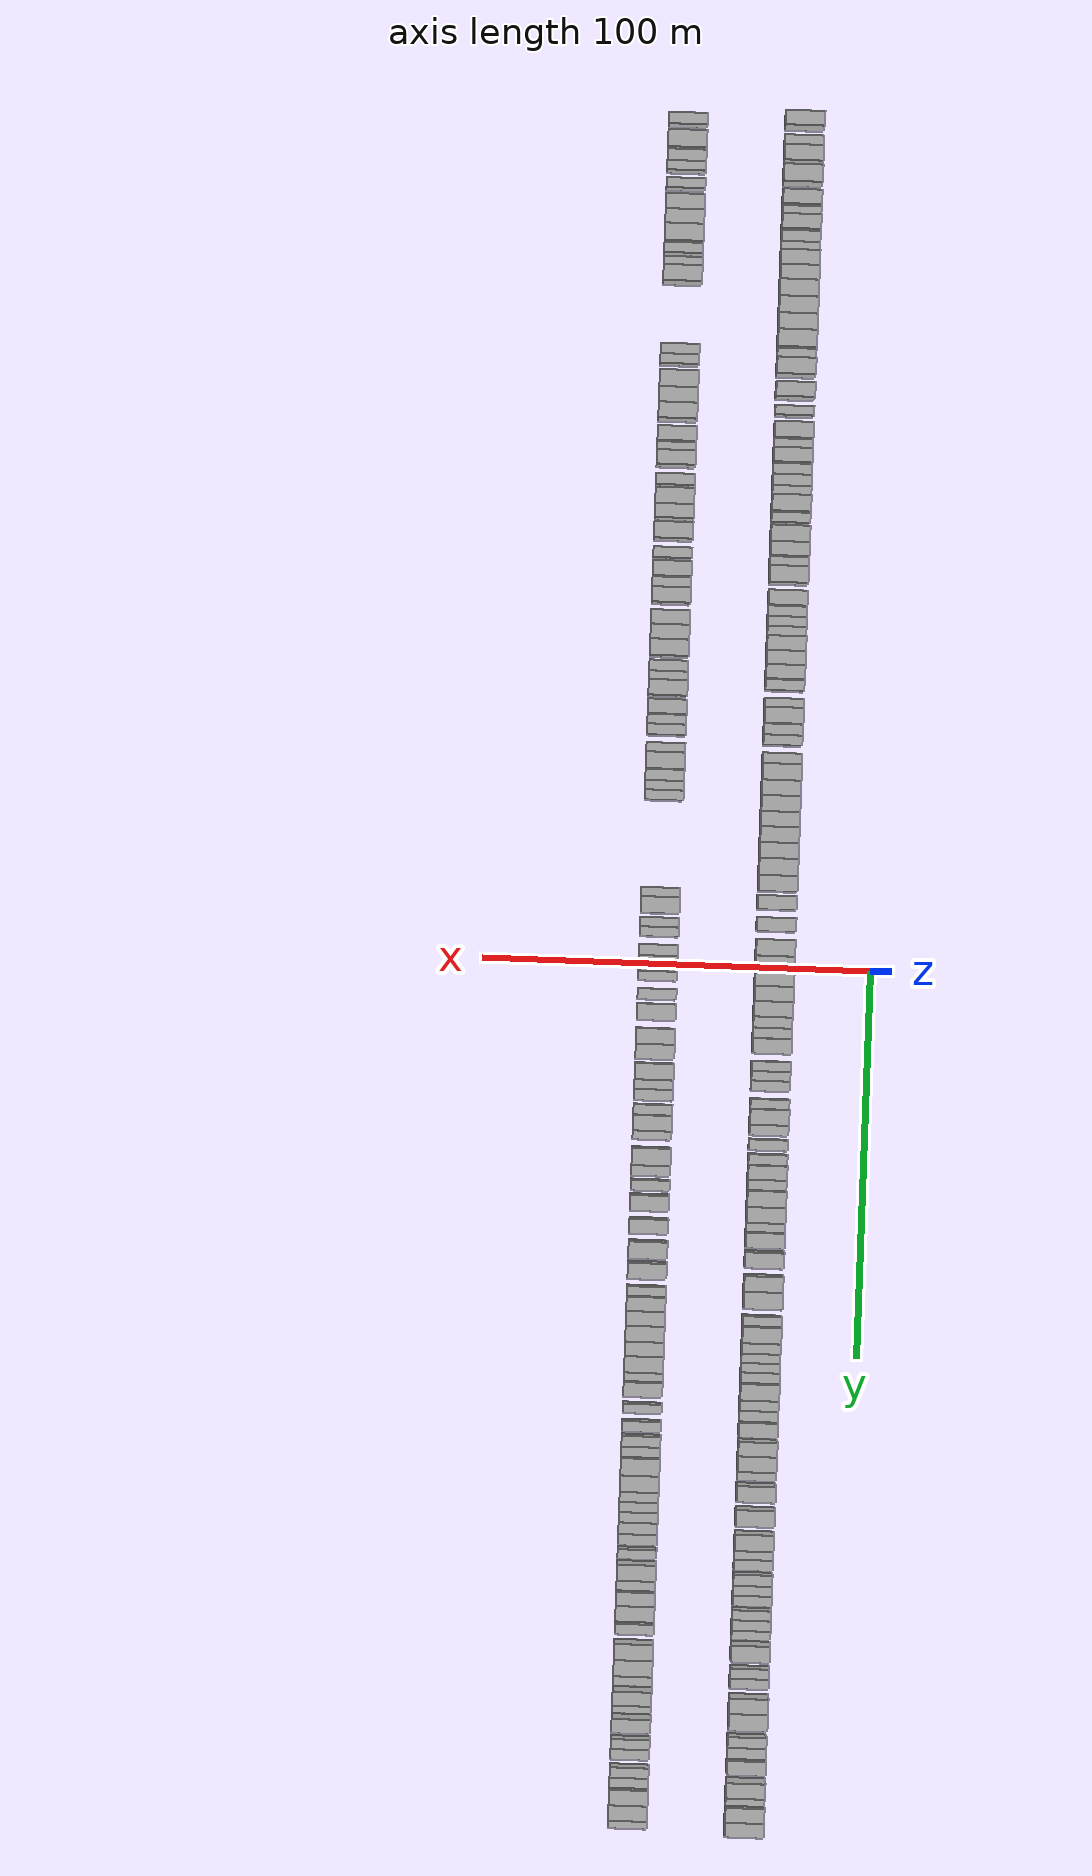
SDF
<sdf version="1.6">
 <world name="default">
  <scene>
   <sky><clouds><speed>12</speed></clouds></sky>
   <ambient>0.4 0.4 0.4 1</ambient>
   <background>0.7 0.7 0.7 1</background>
   <shadows>1</shadows>
  </scene>
  <gravity>0 0 -9.8066</gravity>
  <magnetic_field>6e-06 2.3e-05 -4.2e-05</magnetic_field>
  <physics default="0" name="default_physics" type="ode">
   <ode>
    <solver>
     <type>quick</type>
     <iters>10</iters>
     <sor>1.0</sor>
     <use_dynamic_moi_rescaling>0</use_dynamic_moi_rescaling>
    </solver>
    <constraints>
     <cfm>0</cfm>
     <erp>0.2</erp>
     <contact_max_correcting_vel>100</contact_max_correcting_vel>
     <contact_surface_layer>0.001</contact_surface_layer>
    </constraints>
   </ode>
   <max_step_size>0.004</max_step_size>
   <real_time_factor>1</real_time_factor>
   <real_time_update_rate>250</real_time_update_rate>
  </physics>
  <light name="sun" type="directional">
   <pose>0 0 10 0 0 0</pose>
   <diffuse>0.8 0.8 0.8 1</diffuse>
   <specular>0.2 0.2 0.2 1</specular>
   <attenuation>
    <range>1000</range>
    <constant>0.9</constant>
    <linear>0.01</linear>
    <quadratic>0.001</quadratic>
   </attenuation>
   <direction>-0.5 0.1 -0.9</direction>
  </light>
  <model name="building_1">
   <static>1</static>
   <pose>25.0000 -218.1381 0 0.000000 0.000000 0.000000</pose>
   <link name="link">
    <pose>0 0 4.50 0 0 0</pose>
    <collision name="collision"><geometry><box><size>10.0000 3.7239 9.0000</size></box></geometry></collision>
    <visual name="visual">
     <cast_shadows>0</cast_shadows>
     <geometry><box><size>10.0000 3.7239 9.0000</size></box></geometry>
     <material>
      <script>
       <uri>model://HANNAS_wall/materials/scripts</uri>
       <uri>model://HANNAS_wall/materials/textures</uri>
       <name>vrc/HANNAS_wall</name>
      </script>
     </material>
    </visual>
   </link>
  </model>
  <model name="building_2">
   <static>1</static>
   <pose>25.0000 -212.7857 0 0.000000 0.000000 0.000000</pose>
   <link name="link">
    <pose>0 0 3.00 0 0 0</pose>
    <collision name="collision"><geometry><box><size>10.0000 2.9808 6.0000</size></box></geometry></collision>
    <visual name="visual">
     <cast_shadows>0</cast_shadows>
     <geometry><box><size>10.0000 2.9808 6.0000</size></box></geometry>
     <material>
      <script>
       <uri>model://HANNAS_wall/materials/scripts</uri>
       <uri>model://HANNAS_wall/materials/textures</uri>
       <name>vrc/HANNAS_wall</name>
      </script>
     </material>
    </visual>
   </link>
  </model>
  <model name="building_3">
   <static>1</static>
   <pose>25.0000 -209.2889 0 0.000000 0.000000 0.000000</pose>
   <link name="link">
    <pose>0 0 4.50 0 0 0</pose>
    <collision name="collision"><geometry><box><size>10.0000 4.0128 9.0000</size></box></geometry></collision>
    <visual name="visual">
     <cast_shadows>0</cast_shadows>
     <geometry><box><size>10.0000 4.0128 9.0000</size></box></geometry>
     <material>
      <script>
       <uri>model://HANNAS_wall/materials/scripts</uri>
       <uri>model://HANNAS_wall/materials/textures</uri>
       <name>vrc/HANNAS_wall</name>
      </script>
     </material>
    </visual>
   </link>
  </model>
  <model name="building_4">
   <static>1</static>
   <pose>25.0000 -204.0694 0 0.000000 0.000000 0.000000</pose>
   <link name="link">
    <pose>0 0 4.50 0 0 0</pose>
    <collision name="collision"><geometry><box><size>10.0000 4.4262 9.0000</size></box></geometry></collision>
    <visual name="visual">
     <cast_shadows>0</cast_shadows>
     <geometry><box><size>10.0000 4.4262 9.0000</size></box></geometry>
     <material>
      <script>
       <uri>model://HANNAS_wall/materials/scripts</uri>
       <uri>model://HANNAS_wall/materials/textures</uri>
       <name>vrc/HANNAS_wall</name>
      </script>
     </material>
    </visual>
   </link>
  </model>
  <model name="building_5">
   <static>1</static>
   <pose>25.0000 -197.9782 0 0.000000 0.000000 0.000000</pose>
   <link name="link">
    <pose>0 0 4.50 0 0 0</pose>
    <collision name="collision"><geometry><box><size>10.0000 3.7562 9.0000</size></box></geometry></collision>
    <visual name="visual">
     <cast_shadows>0</cast_shadows>
     <geometry><box><size>10.0000 3.7562 9.0000</size></box></geometry>
     <material>
      <script>
       <uri>model://HANNAS_wall/materials/scripts</uri>
       <uri>model://HANNAS_wall/materials/textures</uri>
       <name>vrc/HANNAS_wall</name>
      </script>
     </material>
    </visual>
   </link>
  </model>
  <model name="building_6">
   <static>1</static>
   <pose>25.0000 -194.8246 0 0.000000 0.000000 0.000000</pose>
   <link name="link">
    <pose>0 0 3.00 0 0 0</pose>
    <collision name="collision"><geometry><box><size>10.0000 2.5508 6.0000</size></box></geometry></collision>
    <visual name="visual">
     <cast_shadows>0</cast_shadows>
     <geometry><box><size>10.0000 2.5508 6.0000</size></box></geometry>
     <material>
      <script>
       <uri>model://HANNAS_wall/materials/scripts</uri>
       <uri>model://HANNAS_wall/materials/textures</uri>
       <name>vrc/HANNAS_wall</name>
      </script>
     </material>
    </visual>
   </link>
  </model>
  <model name="building_7">
   <static>1</static>
   <pose>25.0000 -191.6689 0 0.000000 0.000000 0.000000</pose>
   <link name="link">
    <pose>0 0 4.50 0 0 0</pose>
    <collision name="collision"><geometry><box><size>10.0000 3.7607 9.0000</size></box></geometry></collision>
    <visual name="visual">
     <cast_shadows>0</cast_shadows>
     <geometry><box><size>10.0000 3.7607 9.0000</size></box></geometry>
     <material>
      <script>
       <uri>model://HANNAS_wall/materials/scripts</uri>
       <uri>model://HANNAS_wall/materials/textures</uri>
       <name>vrc/HANNAS_wall</name>
      </script>
     </material>
    </visual>
   </link>
  </model>
  <model name="building_8">
   <static>1</static>
   <pose>25.0000 -188.3491 0 0.000000 0.000000 0.000000</pose>
   <link name="link">
    <pose>0 0 3.00 0 0 0</pose>
    <collision name="collision"><geometry><box><size>10.0000 2.8788 6.0000</size></box></geometry></collision>
    <visual name="visual">
     <cast_shadows>0</cast_shadows>
     <geometry><box><size>10.0000 2.8788 6.0000</size></box></geometry>
     <material>
      <script>
       <uri>model://HANNAS_wall/materials/scripts</uri>
       <uri>model://HANNAS_wall/materials/textures</uri>
       <name>vrc/HANNAS_wall</name>
      </script>
     </material>
    </visual>
   </link>
  </model>
  <model name="building_9">
   <static>1</static>
   <pose>25.0000 -185.6596 0 0.000000 0.000000 0.000000</pose>
   <link name="link">
    <pose>0 0 3.00 0 0 0</pose>
    <collision name="collision"><geometry><box><size>10.0000 2.5003 6.0000</size></box></geometry></collision>
    <visual name="visual">
     <cast_shadows>0</cast_shadows>
     <geometry><box><size>10.0000 2.5003 6.0000</size></box></geometry>
     <material>
      <script>
       <uri>model://HANNAS_wall/materials/scripts</uri>
       <uri>model://HANNAS_wall/materials/textures</uri>
       <name>vrc/HANNAS_wall</name>
      </script>
     </material>
    </visual>
   </link>
  </model>
  <model name="building_10">
   <static>1</static>
   <pose>25.0000 -182.4917 0 0.000000 0.000000 0.000000</pose>
   <link name="link">
    <pose>0 0 4.50 0 0 0</pose>
    <collision name="collision"><geometry><box><size>10.0000 3.8355 9.0000</size></box></geometry></collision>
    <visual name="visual">
     <cast_shadows>0</cast_shadows>
     <geometry><box><size>10.0000 3.8355 9.0000</size></box></geometry>
     <material>
      <script>
       <uri>model://HANNAS_wall/materials/scripts</uri>
       <uri>model://HANNAS_wall/materials/textures</uri>
       <name>vrc/HANNAS_wall</name>
      </script>
     </material>
    </visual>
   </link>
  </model>
  <model name="building_11">
   <static>1</static>
   <pose>25.0000 -178.6902 0 0.000000 0.000000 0.000000</pose>
   <link name="link">
    <pose>0 0 4.50 0 0 0</pose>
    <collision name="collision"><geometry><box><size>10.0000 3.7673 9.0000</size></box></geometry></collision>
    <visual name="visual">
     <cast_shadows>0</cast_shadows>
     <geometry><box><size>10.0000 3.7673 9.0000</size></box></geometry>
     <material>
      <script>
       <uri>model://HANNAS_wall/materials/scripts</uri>
       <uri>model://HANNAS_wall/materials/textures</uri>
       <name>vrc/HANNAS_wall</name>
      </script>
     </material>
    </visual>
   </link>
  </model>
  <model name="building_12">
   <static>1</static>
   <pose>25.0000 -174.6335 0 0.000000 0.000000 0.000000</pose>
   <link name="link">
    <pose>0 0 4.50 0 0 0</pose>
    <collision name="collision"><geometry><box><size>10.0000 4.3462 9.0000</size></box></geometry></collision>
    <visual name="visual">
     <cast_shadows>0</cast_shadows>
     <geometry><box><size>10.0000 4.3462 9.0000</size></box></geometry>
     <material>
      <script>
       <uri>model://HANNAS_wall/materials/scripts</uri>
       <uri>model://HANNAS_wall/materials/textures</uri>
       <name>vrc/HANNAS_wall</name>
      </script>
     </material>
    </visual>
   </link>
  </model>
  <model name="building_13">
   <static>1</static>
   <pose>25.0000 -170.2885 0 0.000000 0.000000 0.000000</pose>
   <link name="link">
    <pose>0 0 4.50 0 0 0</pose>
    <collision name="collision"><geometry><box><size>10.0000 4.3437 9.0000</size></box></geometry></collision>
    <visual name="visual">
     <cast_shadows>0</cast_shadows>
     <geometry><box><size>10.0000 4.3437 9.0000</size></box></geometry>
     <material>
      <script>
       <uri>model://HANNAS_wall/materials/scripts</uri>
       <uri>model://HANNAS_wall/materials/textures</uri>
       <name>vrc/HANNAS_wall</name>
      </script>
     </material>
    </visual>
   </link>
  </model>
  <model name="building_14">
   <static>1</static>
   <pose>25.0000 -166.0444 0 0.000000 0.000000 0.000000</pose>
   <link name="link">
    <pose>0 0 4.50 0 0 0</pose>
    <collision name="collision"><geometry><box><size>10.0000 4.1443 9.0000</size></box></geometry></collision>
    <visual name="visual">
     <cast_shadows>0</cast_shadows>
     <geometry><box><size>10.0000 4.1443 9.0000</size></box></geometry>
     <material>
      <script>
       <uri>model://HANNAS_wall/materials/scripts</uri>
       <uri>model://HANNAS_wall/materials/textures</uri>
       <name>vrc/HANNAS_wall</name>
      </script>
     </material>
    </visual>
   </link>
  </model>
  <model name="building_15">
   <static>1</static>
   <pose>25.0000 -161.7334 0 0.000000 0.000000 0.000000</pose>
   <link name="link">
    <pose>0 0 4.50 0 0 0</pose>
    <collision name="collision"><geometry><box><size>10.0000 4.4777 9.0000</size></box></geometry></collision>
    <visual name="visual">
     <cast_shadows>0</cast_shadows>
     <geometry><box><size>10.0000 4.4777 9.0000</size></box></geometry>
     <material>
      <script>
       <uri>model://HANNAS_wall/materials/scripts</uri>
       <uri>model://HANNAS_wall/materials/textures</uri>
       <name>vrc/HANNAS_wall</name>
      </script>
     </material>
    </visual>
   </link>
  </model>
  <model name="building_16">
   <static>1</static>
   <pose>25.0000 -158.1381 0 0.000000 0.000000 0.000000</pose>
   <link name="link">
    <pose>0 0 3.00 0 0 0</pose>
    <collision name="collision"><geometry><box><size>10.0000 2.7131 6.0000</size></box></geometry></collision>
    <visual name="visual">
     <cast_shadows>0</cast_shadows>
     <geometry><box><size>10.0000 2.7131 6.0000</size></box></geometry>
     <material>
      <script>
       <uri>model://HANNAS_wall/materials/scripts</uri>
       <uri>model://HANNAS_wall/materials/textures</uri>
       <name>vrc/HANNAS_wall</name>
      </script>
     </material>
    </visual>
   </link>
  </model>
  <model name="building_17">
   <static>1</static>
   <pose>25.0000 -154.6618 0 0.000000 0.000000 0.000000</pose>
   <link name="link">
    <pose>0 0 4.50 0 0 0</pose>
    <collision name="collision"><geometry><box><size>10.0000 4.2395 9.0000</size></box></geometry></collision>
    <visual name="visual">
     <cast_shadows>0</cast_shadows>
     <geometry><box><size>10.0000 4.2395 9.0000</size></box></geometry>
     <material>
      <script>
       <uri>model://HANNAS_wall/materials/scripts</uri>
       <uri>model://HANNAS_wall/materials/textures</uri>
       <name>vrc/HANNAS_wall</name>
      </script>
     </material>
    </visual>
   </link>
  </model>
  <model name="building_18">
   <static>1</static>
   <pose>25.0000 -148.6425 0 0.000000 0.000000 0.000000</pose>
   <link name="link">
    <pose>0 0 4.50 0 0 0</pose>
    <collision name="collision"><geometry><box><size>10.0000 3.7990 9.0000</size></box></geometry></collision>
    <visual name="visual">
     <cast_shadows>0</cast_shadows>
     <geometry><box><size>10.0000 3.7990 9.0000</size></box></geometry>
     <material>
      <script>
       <uri>model://HANNAS_wall/materials/scripts</uri>
       <uri>model://HANNAS_wall/materials/textures</uri>
       <name>vrc/HANNAS_wall</name>
      </script>
     </material>
    </visual>
   </link>
  </model>
  <model name="building_19">
   <static>1</static>
   <pose>25.0000 -143.5411 0 0.000000 0.000000 0.000000</pose>
   <link name="link">
    <pose>0 0 3.00 0 0 0</pose>
    <collision name="collision"><geometry><box><size>10.0000 2.4039 6.0000</size></box></geometry></collision>
    <visual name="visual">
     <cast_shadows>0</cast_shadows>
     <geometry><box><size>10.0000 2.4039 6.0000</size></box></geometry>
     <material>
      <script>
       <uri>model://HANNAS_wall/materials/scripts</uri>
       <uri>model://HANNAS_wall/materials/textures</uri>
       <name>vrc/HANNAS_wall</name>
      </script>
     </material>
    </visual>
   </link>
  </model>
  <model name="building_20">
   <static>1</static>
   <pose>25.0000 -138.2847 0 0.000000 0.000000 0.000000</pose>
   <link name="link">
    <pose>0 0 4.50 0 0 0</pose>
    <collision name="collision"><geometry><box><size>10.0000 4.1088 9.0000</size></box></geometry></collision>
    <visual name="visual">
     <cast_shadows>0</cast_shadows>
     <geometry><box><size>10.0000 4.1088 9.0000</size></box></geometry>
     <material>
      <script>
       <uri>model://HANNAS_wall/materials/scripts</uri>
       <uri>model://HANNAS_wall/materials/textures</uri>
       <name>vrc/HANNAS_wall</name>
      </script>
     </material>
    </visual>
   </link>
  </model>
  <model name="building_21">
   <static>1</static>
   <pose>25.0000 -134.9538 0 0.000000 0.000000 0.000000</pose>
   <link name="link">
    <pose>0 0 3.00 0 0 0</pose>
    <collision name="collision"><geometry><box><size>10.0000 2.5530 6.0000</size></box></geometry></collision>
    <visual name="visual">
     <cast_shadows>0</cast_shadows>
     <geometry><box><size>10.0000 2.5530 6.0000</size></box></geometry>
     <material>
      <script>
       <uri>model://HANNAS_wall/materials/scripts</uri>
       <uri>model://HANNAS_wall/materials/textures</uri>
       <name>vrc/HANNAS_wall</name>
      </script>
     </material>
    </visual>
   </link>
  </model>
  <model name="building_22">
   <static>1</static>
   <pose>25.0000 -131.8000 0 0.000000 0.000000 0.000000</pose>
   <link name="link">
    <pose>0 0 4.50 0 0 0</pose>
    <collision name="collision"><geometry><box><size>10.0000 3.7545 9.0000</size></box></geometry></collision>
    <visual name="visual">
     <cast_shadows>0</cast_shadows>
     <geometry><box><size>10.0000 3.7545 9.0000</size></box></geometry>
     <material>
      <script>
       <uri>model://HANNAS_wall/materials/scripts</uri>
       <uri>model://HANNAS_wall/materials/textures</uri>
       <name>vrc/HANNAS_wall</name>
      </script>
     </material>
    </visual>
   </link>
  </model>
  <model name="building_23">
   <static>1</static>
   <pose>25.0000 -128.5241 0 0.000000 0.000000 0.000000</pose>
   <link name="link">
    <pose>0 0 3.00 0 0 0</pose>
    <collision name="collision"><geometry><box><size>10.0000 2.7974 6.0000</size></box></geometry></collision>
    <visual name="visual">
     <cast_shadows>0</cast_shadows>
     <geometry><box><size>10.0000 2.7974 6.0000</size></box></geometry>
     <material>
      <script>
       <uri>model://HANNAS_wall/materials/scripts</uri>
       <uri>model://HANNAS_wall/materials/textures</uri>
       <name>vrc/HANNAS_wall</name>
      </script>
     </material>
    </visual>
   </link>
  </model>
  <model name="building_24">
   <static>1</static>
   <pose>25.0000 -125.6528 0 0.000000 0.000000 0.000000</pose>
   <link name="link">
    <pose>0 0 3.00 0 0 0</pose>
    <collision name="collision"><geometry><box><size>10.0000 2.9451 6.0000</size></box></geometry></collision>
    <visual name="visual">
     <cast_shadows>0</cast_shadows>
     <geometry><box><size>10.0000 2.9451 6.0000</size></box></geometry>
     <material>
      <script>
       <uri>model://HANNAS_wall/materials/scripts</uri>
       <uri>model://HANNAS_wall/materials/textures</uri>
       <name>vrc/HANNAS_wall</name>
      </script>
     </material>
    </visual>
   </link>
  </model>
  <model name="building_25">
   <static>1</static>
   <pose>25.0000 -122.9113 0 0.000000 0.000000 0.000000</pose>
   <link name="link">
    <pose>0 0 3.00 0 0 0</pose>
    <collision name="collision"><geometry><box><size>10.0000 2.5378 6.0000</size></box></geometry></collision>
    <visual name="visual">
     <cast_shadows>0</cast_shadows>
     <geometry><box><size>10.0000 2.5378 6.0000</size></box></geometry>
     <material>
      <script>
       <uri>model://HANNAS_wall/materials/scripts</uri>
       <uri>model://HANNAS_wall/materials/textures</uri>
       <name>vrc/HANNAS_wall</name>
      </script>
     </material>
    </visual>
   </link>
  </model>
  <model name="building_26">
   <static>1</static>
   <pose>25.0000 -119.5034 0 0.000000 0.000000 0.000000</pose>
   <link name="link">
    <pose>0 0 4.50 0 0 0</pose>
    <collision name="collision"><geometry><box><size>10.0000 4.2780 9.0000</size></box></geometry></collision>
    <visual name="visual">
     <cast_shadows>0</cast_shadows>
     <geometry><box><size>10.0000 4.2780 9.0000</size></box></geometry>
     <material>
      <script>
       <uri>model://HANNAS_wall/materials/scripts</uri>
       <uri>model://HANNAS_wall/materials/textures</uri>
       <name>vrc/HANNAS_wall</name>
      </script>
     </material>
    </visual>
   </link>
  </model>
  <model name="building_27">
   <static>1</static>
   <pose>25.0000 -116.0548 0 0.000000 0.000000 0.000000</pose>
   <link name="link">
    <pose>0 0 3.00 0 0 0</pose>
    <collision name="collision"><geometry><box><size>10.0000 2.6193 6.0000</size></box></geometry></collision>
    <visual name="visual">
     <cast_shadows>0</cast_shadows>
     <geometry><box><size>10.0000 2.6193 6.0000</size></box></geometry>
     <material>
      <script>
       <uri>model://HANNAS_wall/materials/scripts</uri>
       <uri>model://HANNAS_wall/materials/textures</uri>
       <name>vrc/HANNAS_wall</name>
      </script>
     </material>
    </visual>
   </link>
  </model>
  <model name="building_28">
   <static>1</static>
   <pose>25.0000 -111.6544 0 0.000000 0.000000 0.000000</pose>
   <link name="link">
    <pose>0 0 4.50 0 0 0</pose>
    <collision name="collision"><geometry><box><size>10.0000 4.1814 9.0000</size></box></geometry></collision>
    <visual name="visual">
     <cast_shadows>0</cast_shadows>
     <geometry><box><size>10.0000 4.1814 9.0000</size></box></geometry>
     <material>
      <script>
       <uri>model://HANNAS_wall/materials/scripts</uri>
       <uri>model://HANNAS_wall/materials/textures</uri>
       <name>vrc/HANNAS_wall</name>
      </script>
     </material>
    </visual>
   </link>
  </model>
  <model name="building_29">
   <static>1</static>
   <pose>25.0000 -107.7381 0 0.000000 0.000000 0.000000</pose>
   <link name="link">
    <pose>0 0 4.50 0 0 0</pose>
    <collision name="collision"><geometry><box><size>10.0000 3.6512 9.0000</size></box></geometry></collision>
    <visual name="visual">
     <cast_shadows>0</cast_shadows>
     <geometry><box><size>10.0000 3.6512 9.0000</size></box></geometry>
     <material>
      <script>
       <uri>model://HANNAS_wall/materials/scripts</uri>
       <uri>model://HANNAS_wall/materials/textures</uri>
       <name>vrc/HANNAS_wall</name>
      </script>
     </material>
    </visual>
   </link>
  </model>
  <model name="building_30">
   <static>1</static>
   <pose>25.0000 -104.6395 0 0.000000 0.000000 0.000000</pose>
   <link name="link">
    <pose>0 0 3.00 0 0 0</pose>
    <collision name="collision"><geometry><box><size>10.0000 2.5461 6.0000</size></box></geometry></collision>
    <visual name="visual">
     <cast_shadows>0</cast_shadows>
     <geometry><box><size>10.0000 2.5461 6.0000</size></box></geometry>
     <material>
      <script>
       <uri>model://HANNAS_wall/materials/scripts</uri>
       <uri>model://HANNAS_wall/materials/textures</uri>
       <name>vrc/HANNAS_wall</name>
      </script>
     </material>
    </visual>
   </link>
  </model>
  <model name="building_31">
   <static>1</static>
   <pose>25.0000 -101.2330 0 0.000000 0.000000 0.000000</pose>
   <link name="link">
    <pose>0 0 4.50 0 0 0</pose>
    <collision name="collision"><geometry><box><size>10.0000 4.2669 9.0000</size></box></geometry></collision>
    <visual name="visual">
     <cast_shadows>0</cast_shadows>
     <geometry><box><size>10.0000 4.2669 9.0000</size></box></geometry>
     <material>
      <script>
       <uri>model://HANNAS_wall/materials/scripts</uri>
       <uri>model://HANNAS_wall/materials/textures</uri>
       <name>vrc/HANNAS_wall</name>
      </script>
     </material>
    </visual>
   </link>
  </model>
  <model name="building_32">
   <static>1</static>
   <pose>25.0000 -95.1772 0 0.000000 0.000000 0.000000</pose>
   <link name="link">
    <pose>0 0 4.50 0 0 0</pose>
    <collision name="collision"><geometry><box><size>10.0000 3.8447 9.0000</size></box></geometry></collision>
    <visual name="visual">
     <cast_shadows>0</cast_shadows>
     <geometry><box><size>10.0000 3.8447 9.0000</size></box></geometry>
     <material>
      <script>
       <uri>model://HANNAS_wall/materials/scripts</uri>
       <uri>model://HANNAS_wall/materials/textures</uri>
       <name>vrc/HANNAS_wall</name>
      </script>
     </material>
    </visual>
   </link>
  </model>
  <model name="building_33">
   <static>1</static>
   <pose>25.0000 -91.9162 0 0.000000 0.000000 0.000000</pose>
   <link name="link">
    <pose>0 0 3.00 0 0 0</pose>
    <collision name="collision"><geometry><box><size>10.0000 2.6773 6.0000</size></box></geometry></collision>
    <visual name="visual">
     <cast_shadows>0</cast_shadows>
     <geometry><box><size>10.0000 2.6773 6.0000</size></box></geometry>
     <material>
      <script>
       <uri>model://HANNAS_wall/materials/scripts</uri>
       <uri>model://HANNAS_wall/materials/textures</uri>
       <name>vrc/HANNAS_wall</name>
      </script>
     </material>
    </visual>
   </link>
  </model>
  <model name="building_34">
   <static>1</static>
   <pose>25.0000 -89.3079 0 0.000000 0.000000 0.000000</pose>
   <link name="link">
    <pose>0 0 3.00 0 0 0</pose>
    <collision name="collision"><geometry><box><size>10.0000 2.5394 6.0000</size></box></geometry></collision>
    <visual name="visual">
     <cast_shadows>0</cast_shadows>
     <geometry><box><size>10.0000 2.5394 6.0000</size></box></geometry>
     <material>
      <script>
       <uri>model://HANNAS_wall/materials/scripts</uri>
       <uri>model://HANNAS_wall/materials/textures</uri>
       <name>vrc/HANNAS_wall</name>
      </script>
     </material>
    </visual>
   </link>
  </model>
  <model name="building_35">
   <static>1</static>
   <pose>25.0000 -86.7060 0 0.000000 0.000000 0.000000</pose>
   <link name="link">
    <pose>0 0 3.00 0 0 0</pose>
    <collision name="collision"><geometry><box><size>10.0000 2.6643 6.0000</size></box></geometry></collision>
    <visual name="visual">
     <cast_shadows>0</cast_shadows>
     <geometry><box><size>10.0000 2.6643 6.0000</size></box></geometry>
     <material>
      <script>
       <uri>model://HANNAS_wall/materials/scripts</uri>
       <uri>model://HANNAS_wall/materials/textures</uri>
       <name>vrc/HANNAS_wall</name>
      </script>
     </material>
    </visual>
   </link>
  </model>
  <model name="building_36">
   <static>1</static>
   <pose>25.0000 -83.5017 0 0.000000 0.000000 0.000000</pose>
   <link name="link">
    <pose>0 0 4.50 0 0 0</pose>
    <collision name="collision"><geometry><box><size>10.0000 3.7444 9.0000</size></box></geometry></collision>
    <visual name="visual">
     <cast_shadows>0</cast_shadows>
     <geometry><box><size>10.0000 3.7444 9.0000</size></box></geometry>
     <material>
      <script>
       <uri>model://HANNAS_wall/materials/scripts</uri>
       <uri>model://HANNAS_wall/materials/textures</uri>
       <name>vrc/HANNAS_wall</name>
      </script>
     </material>
    </visual>
   </link>
  </model>
  <model name="building_37">
   <static>1</static>
   <pose>25.0000 -79.8183 0 0.000000 0.000000 0.000000</pose>
   <link name="link">
    <pose>0 0 4.50 0 0 0</pose>
    <collision name="collision"><geometry><box><size>10.0000 3.6223 9.0000</size></box></geometry></collision>
    <visual name="visual">
     <cast_shadows>0</cast_shadows>
     <geometry><box><size>10.0000 3.6223 9.0000</size></box></geometry>
     <material>
      <script>
       <uri>model://HANNAS_wall/materials/scripts</uri>
       <uri>model://HANNAS_wall/materials/textures</uri>
       <name>vrc/HANNAS_wall</name>
      </script>
     </material>
    </visual>
   </link>
  </model>
  <model name="building_38">
   <static>1</static>
   <pose>25.0000 -76.1771 0 0.000000 0.000000 0.000000</pose>
   <link name="link">
    <pose>0 0 4.50 0 0 0</pose>
    <collision name="collision"><geometry><box><size>10.0000 3.6602 9.0000</size></box></geometry></collision>
    <visual name="visual">
     <cast_shadows>0</cast_shadows>
     <geometry><box><size>10.0000 3.6602 9.0000</size></box></geometry>
     <material>
      <script>
       <uri>model://HANNAS_wall/materials/scripts</uri>
       <uri>model://HANNAS_wall/materials/textures</uri>
       <name>vrc/HANNAS_wall</name>
      </script>
     </material>
    </visual>
   </link>
  </model>
  <model name="building_39">
   <static>1</static>
   <pose>25.0000 -72.9462 0 0.000000 0.000000 0.000000</pose>
   <link name="link">
    <pose>0 0 3.00 0 0 0</pose>
    <collision name="collision"><geometry><box><size>10.0000 2.8016 6.0000</size></box></geometry></collision>
    <visual name="visual">
     <cast_shadows>0</cast_shadows>
     <geometry><box><size>10.0000 2.8016 6.0000</size></box></geometry>
     <material>
      <script>
       <uri>model://HANNAS_wall/materials/scripts</uri>
       <uri>model://HANNAS_wall/materials/textures</uri>
       <name>vrc/HANNAS_wall</name>
      </script>
     </material>
    </visual>
   </link>
  </model>
  <model name="building_40">
   <static>1</static>
   <pose>25.0000 -68.3101 0 0.000000 0.000000 0.000000</pose>
   <link name="link">
    <pose>0 0 3.00 0 0 0</pose>
    <collision name="collision"><geometry><box><size>10.0000 2.4704 6.0000</size></box></geometry></collision>
    <visual name="visual">
     <cast_shadows>0</cast_shadows>
     <geometry><box><size>10.0000 2.4704 6.0000</size></box></geometry>
     <material>
      <script>
       <uri>model://HANNAS_wall/materials/scripts</uri>
       <uri>model://HANNAS_wall/materials/textures</uri>
       <name>vrc/HANNAS_wall</name>
      </script>
     </material>
    </visual>
   </link>
  </model>
  <model name="building_41">
   <static>1</static>
   <pose>25.0000 -65.0184 0 0.000000 0.000000 0.000000</pose>
   <link name="link">
    <pose>0 0 4.50 0 0 0</pose>
    <collision name="collision"><geometry><box><size>10.0000 4.1132 9.0000</size></box></geometry></collision>
    <visual name="visual">
     <cast_shadows>0</cast_shadows>
     <geometry><box><size>10.0000 4.1132 9.0000</size></box></geometry>
     <material>
      <script>
       <uri>model://HANNAS_wall/materials/scripts</uri>
       <uri>model://HANNAS_wall/materials/textures</uri>
       <name>vrc/HANNAS_wall</name>
      </script>
     </material>
    </visual>
   </link>
  </model>
  <model name="building_42">
   <static>1</static>
   <pose>25.0000 -61.5409 0 0.000000 0.000000 0.000000</pose>
   <link name="link">
    <pose>0 0 3.00 0 0 0</pose>
    <collision name="collision"><geometry><box><size>10.0000 2.8418 6.0000</size></box></geometry></collision>
    <visual name="visual">
     <cast_shadows>0</cast_shadows>
     <geometry><box><size>10.0000 2.8418 6.0000</size></box></geometry>
     <material>
      <script>
       <uri>model://HANNAS_wall/materials/scripts</uri>
       <uri>model://HANNAS_wall/materials/textures</uri>
       <name>vrc/HANNAS_wall</name>
      </script>
     </material>
    </visual>
   </link>
  </model>
  <model name="building_43">
   <static>1</static>
   <pose>25.0000 -58.7988 0 0.000000 0.000000 0.000000</pose>
   <link name="link">
    <pose>0 0 3.00 0 0 0</pose>
    <collision name="collision"><geometry><box><size>10.0000 2.6424 6.0000</size></box></geometry></collision>
    <visual name="visual">
     <cast_shadows>0</cast_shadows>
     <geometry><box><size>10.0000 2.6424 6.0000</size></box></geometry>
     <material>
      <script>
       <uri>model://HANNAS_wall/materials/scripts</uri>
       <uri>model://HANNAS_wall/materials/textures</uri>
       <name>vrc/HANNAS_wall</name>
      </script>
     </material>
    </visual>
   </link>
  </model>
  <model name="building_44">
   <static>1</static>
   <pose>25.0000 -54.0521 0 0.000000 0.000000 0.000000</pose>
   <link name="link">
    <pose>0 0 3.00 0 0 0</pose>
    <collision name="collision"><geometry><box><size>10.0000 2.8510 6.0000</size></box></geometry></collision>
    <visual name="visual">
     <cast_shadows>0</cast_shadows>
     <geometry><box><size>10.0000 2.8510 6.0000</size></box></geometry>
     <material>
      <script>
       <uri>model://HANNAS_wall/materials/scripts</uri>
       <uri>model://HANNAS_wall/materials/textures</uri>
       <name>vrc/HANNAS_wall</name>
      </script>
     </material>
    </visual>
   </link>
  </model>
  <model name="building_45">
   <static>1</static>
   <pose>25.0000 -50.5195 0 0.000000 0.000000 0.000000</pose>
   <link name="link">
    <pose>0 0 4.50 0 0 0</pose>
    <collision name="collision"><geometry><box><size>10.0000 4.2141 9.0000</size></box></geometry></collision>
    <visual name="visual">
     <cast_shadows>0</cast_shadows>
     <geometry><box><size>10.0000 4.2141 9.0000</size></box></geometry>
     <material>
      <script>
       <uri>model://HANNAS_wall/materials/scripts</uri>
       <uri>model://HANNAS_wall/materials/textures</uri>
       <name>vrc/HANNAS_wall</name>
      </script>
     </material>
    </visual>
   </link>
  </model>
  <model name="building_46">
   <static>1</static>
   <pose>25.0000 -46.4280 0 0.000000 0.000000 0.000000</pose>
   <link name="link">
    <pose>0 0 4.50 0 0 0</pose>
    <collision name="collision"><geometry><box><size>10.0000 3.9689 9.0000</size></box></geometry></collision>
    <visual name="visual">
     <cast_shadows>0</cast_shadows>
     <geometry><box><size>10.0000 3.9689 9.0000</size></box></geometry>
     <material>
      <script>
       <uri>model://HANNAS_wall/materials/scripts</uri>
       <uri>model://HANNAS_wall/materials/textures</uri>
       <name>vrc/HANNAS_wall</name>
      </script>
     </material>
    </visual>
   </link>
  </model>
  <model name="building_47">
   <static>1</static>
   <pose>25.0000 -42.3883 0 0.000000 0.000000 0.000000</pose>
   <link name="link">
    <pose>0 0 4.50 0 0 0</pose>
    <collision name="collision"><geometry><box><size>10.0000 4.1106 9.0000</size></box></geometry></collision>
    <visual name="visual">
     <cast_shadows>0</cast_shadows>
     <geometry><box><size>10.0000 4.1106 9.0000</size></box></geometry>
     <material>
      <script>
       <uri>model://HANNAS_wall/materials/scripts</uri>
       <uri>model://HANNAS_wall/materials/textures</uri>
       <name>vrc/HANNAS_wall</name>
      </script>
     </material>
    </visual>
   </link>
  </model>
  <model name="building_48">
   <static>1</static>
   <pose>25.0000 -38.3885 0 0.000000 0.000000 0.000000</pose>
   <link name="link">
    <pose>0 0 4.50 0 0 0</pose>
    <collision name="collision"><geometry><box><size>10.0000 3.8890 9.0000</size></box></geometry></collision>
    <visual name="visual">
     <cast_shadows>0</cast_shadows>
     <geometry><box><size>10.0000 3.8890 9.0000</size></box></geometry>
     <material>
      <script>
       <uri>model://HANNAS_wall/materials/scripts</uri>
       <uri>model://HANNAS_wall/materials/textures</uri>
       <name>vrc/HANNAS_wall</name>
      </script>
     </material>
    </visual>
   </link>
  </model>
  <model name="building_49">
   <static>1</static>
   <pose>25.0000 -34.4165 0 0.000000 0.000000 0.000000</pose>
   <link name="link">
    <pose>0 0 4.50 0 0 0</pose>
    <collision name="collision"><geometry><box><size>10.0000 4.0550 9.0000</size></box></geometry></collision>
    <visual name="visual">
     <cast_shadows>0</cast_shadows>
     <geometry><box><size>10.0000 4.0550 9.0000</size></box></geometry>
     <material>
      <script>
       <uri>model://HANNAS_wall/materials/scripts</uri>
       <uri>model://HANNAS_wall/materials/textures</uri>
       <name>vrc/HANNAS_wall</name>
      </script>
     </material>
    </visual>
   </link>
  </model>
  <model name="building_50">
   <static>1</static>
   <pose>25.0000 -30.3690 0 0.000000 0.000000 0.000000</pose>
   <link name="link">
    <pose>0 0 4.50 0 0 0</pose>
    <collision name="collision"><geometry><box><size>10.0000 4.0399 9.0000</size></box></geometry></collision>
    <visual name="visual">
     <cast_shadows>0</cast_shadows>
     <geometry><box><size>10.0000 4.0399 9.0000</size></box></geometry>
     <material>
      <script>
       <uri>model://HANNAS_wall/materials/scripts</uri>
       <uri>model://HANNAS_wall/materials/textures</uri>
       <name>vrc/HANNAS_wall</name>
      </script>
     </material>
    </visual>
   </link>
  </model>
  <model name="building_51">
   <static>1</static>
   <pose>25.0000 -26.1624 0 0.000000 0.000000 0.000000</pose>
   <link name="link">
    <pose>0 0 4.50 0 0 0</pose>
    <collision name="collision"><geometry><box><size>10.0000 4.3732 9.0000</size></box></geometry></collision>
    <visual name="visual">
     <cast_shadows>0</cast_shadows>
     <geometry><box><size>10.0000 4.3732 9.0000</size></box></geometry>
     <material>
      <script>
       <uri>model://HANNAS_wall/materials/scripts</uri>
       <uri>model://HANNAS_wall/materials/textures</uri>
       <name>vrc/HANNAS_wall</name>
      </script>
     </material>
    </visual>
   </link>
  </model>
  <model name="building_52">
   <static>1</static>
   <pose>25.0000 -21.8978 0 0.000000 0.000000 0.000000</pose>
   <link name="link">
    <pose>0 0 4.50 0 0 0</pose>
    <collision name="collision"><geometry><box><size>10.0000 4.1560 9.0000</size></box></geometry></collision>
    <visual name="visual">
     <cast_shadows>0</cast_shadows>
     <geometry><box><size>10.0000 4.1560 9.0000</size></box></geometry>
     <material>
      <script>
       <uri>model://HANNAS_wall/materials/scripts</uri>
       <uri>model://HANNAS_wall/materials/textures</uri>
       <name>vrc/HANNAS_wall</name>
      </script>
     </material>
    </visual>
   </link>
  </model>
  <model name="building_53">
   <static>1</static>
   <pose>25.0000 -16.9798 0 0.000000 0.000000 0.000000</pose>
   <link name="link">
    <pose>0 0 4.50 0 0 0</pose>
    <collision name="collision"><geometry><box><size>10.0000 3.6798 9.0000</size></box></geometry></collision>
    <visual name="visual">
     <cast_shadows>0</cast_shadows>
     <geometry><box><size>10.0000 3.6798 9.0000</size></box></geometry>
     <material>
      <script>
       <uri>model://HANNAS_wall/materials/scripts</uri>
       <uri>model://HANNAS_wall/materials/textures</uri>
       <name>vrc/HANNAS_wall</name>
      </script>
     </material>
    </visual>
   </link>
  </model>
  <model name="building_54">
   <static>1</static>
   <pose>25.0000 -11.3338 0 0.000000 0.000000 0.000000</pose>
   <link name="link">
    <pose>0 0 4.50 0 0 0</pose>
    <collision name="collision"><geometry><box><size>10.0000 3.6122 9.0000</size></box></geometry></collision>
    <visual name="visual">
     <cast_shadows>0</cast_shadows>
     <geometry><box><size>10.0000 3.6122 9.0000</size></box></geometry>
     <material>
      <script>
       <uri>model://HANNAS_wall/materials/scripts</uri>
       <uri>model://HANNAS_wall/materials/textures</uri>
       <name>vrc/HANNAS_wall</name>
      </script>
     </material>
    </visual>
   </link>
  </model>
  <model name="building_55">
   <static>1</static>
   <pose>25.0000 -5.4195 0 0.000000 0.000000 0.000000</pose>
   <link name="link">
    <pose>0 0 4.50 0 0 0</pose>
    <collision name="collision"><geometry><box><size>10.0000 4.2166 9.0000</size></box></geometry></collision>
    <visual name="visual">
     <cast_shadows>0</cast_shadows>
     <geometry><box><size>10.0000 4.2166 9.0000</size></box></geometry>
     <material>
      <script>
       <uri>model://HANNAS_wall/materials/scripts</uri>
       <uri>model://HANNAS_wall/materials/textures</uri>
       <name>vrc/HANNAS_wall</name>
      </script>
     </material>
    </visual>
   </link>
  </model>
  <model name="building_56">
   <static>1</static>
   <pose>25.0000 -1.8960 0 0.000000 0.000000 0.000000</pose>
   <link name="link">
    <pose>0 0 3.00 0 0 0</pose>
    <collision name="collision"><geometry><box><size>10.0000 2.8304 6.0000</size></box></geometry></collision>
    <visual name="visual">
     <cast_shadows>0</cast_shadows>
     <geometry><box><size>10.0000 2.8304 6.0000</size></box></geometry>
     <material>
      <script>
       <uri>model://HANNAS_wall/materials/scripts</uri>
       <uri>model://HANNAS_wall/materials/textures</uri>
       <name>vrc/HANNAS_wall</name>
      </script>
     </material>
    </visual>
   </link>
  </model>
  <model name="building_57">
   <static>1</static>
   <pose>25.0000 2.4853 0 0.000000 0.000000 0.000000</pose>
   <link name="link">
    <pose>0 0 4.50 0 0 0</pose>
    <collision name="collision"><geometry><box><size>10.0000 3.9321 9.0000</size></box></geometry></collision>
    <visual name="visual">
     <cast_shadows>0</cast_shadows>
     <geometry><box><size>10.0000 3.9321 9.0000</size></box></geometry>
     <material>
      <script>
       <uri>model://HANNAS_wall/materials/scripts</uri>
       <uri>model://HANNAS_wall/materials/textures</uri>
       <name>vrc/HANNAS_wall</name>
      </script>
     </material>
    </visual>
   </link>
  </model>
  <model name="building_58">
   <static>1</static>
   <pose>25.0000 6.4000 0 0.000000 0.000000 0.000000</pose>
   <link name="link">
    <pose>0 0 4.50 0 0 0</pose>
    <collision name="collision"><geometry><box><size>10.0000 3.8975 9.0000</size></box></geometry></collision>
    <visual name="visual">
     <cast_shadows>0</cast_shadows>
     <geometry><box><size>10.0000 3.8975 9.0000</size></box></geometry>
     <material>
      <script>
       <uri>model://HANNAS_wall/materials/scripts</uri>
       <uri>model://HANNAS_wall/materials/textures</uri>
       <name>vrc/HANNAS_wall</name>
      </script>
     </material>
    </visual>
   </link>
  </model>
  <model name="building_59">
   <static>1</static>
   <pose>25.0000 10.3311 0 0.000000 0.000000 0.000000</pose>
   <link name="link">
    <pose>0 0 4.50 0 0 0</pose>
    <collision name="collision"><geometry><box><size>10.0000 3.9646 9.0000</size></box></geometry></collision>
    <visual name="visual">
     <cast_shadows>0</cast_shadows>
     <geometry><box><size>10.0000 3.9646 9.0000</size></box></geometry>
     <material>
      <script>
       <uri>model://HANNAS_wall/materials/scripts</uri>
       <uri>model://HANNAS_wall/materials/textures</uri>
       <name>vrc/HANNAS_wall</name>
      </script>
     </material>
    </visual>
   </link>
  </model>
  <model name="building_60">
   <static>1</static>
   <pose>25.0000 13.7487 0 0.000000 0.000000 0.000000</pose>
   <link name="link">
    <pose>0 0 3.00 0 0 0</pose>
    <collision name="collision"><geometry><box><size>10.0000 2.8707 6.0000</size></box></geometry></collision>
    <visual name="visual">
     <cast_shadows>0</cast_shadows>
     <geometry><box><size>10.0000 2.8707 6.0000</size></box></geometry>
     <material>
      <script>
       <uri>model://HANNAS_wall/materials/scripts</uri>
       <uri>model://HANNAS_wall/materials/textures</uri>
       <name>vrc/HANNAS_wall</name>
      </script>
     </material>
    </visual>
   </link>
  </model>
  <model name="building_61">
   <static>1</static>
   <pose>25.0000 16.5236 0 0.000000 0.000000 0.000000</pose>
   <link name="link">
    <pose>0 0 3.00 0 0 0</pose>
    <collision name="collision"><geometry><box><size>10.0000 2.6791 6.0000</size></box></geometry></collision>
    <visual name="visual">
     <cast_shadows>0</cast_shadows>
     <geometry><box><size>10.0000 2.6791 6.0000</size></box></geometry>
     <material>
      <script>
       <uri>model://HANNAS_wall/materials/scripts</uri>
       <uri>model://HANNAS_wall/materials/textures</uri>
       <name>vrc/HANNAS_wall</name>
      </script>
     </material>
    </visual>
   </link>
  </model>
  <model name="building_62">
   <static>1</static>
   <pose>25.0000 19.8373 0 0.000000 0.000000 0.000000</pose>
   <link name="link">
    <pose>0 0 4.50 0 0 0</pose>
    <collision name="collision"><geometry><box><size>10.0000 3.9483 9.0000</size></box></geometry></collision>
    <visual name="visual">
     <cast_shadows>0</cast_shadows>
     <geometry><box><size>10.0000 3.9483 9.0000</size></box></geometry>
     <material>
      <script>
       <uri>model://HANNAS_wall/materials/scripts</uri>
       <uri>model://HANNAS_wall/materials/textures</uri>
       <name>vrc/HANNAS_wall</name>
      </script>
     </material>
    </visual>
   </link>
  </model>
  <model name="building_63">
   <static>1</static>
   <pose>25.0000 25.0874 0 0.000000 0.000000 0.000000</pose>
   <link name="link">
    <pose>0 0 3.00 0 0 0</pose>
    <collision name="collision"><geometry><box><size>10.0000 2.5519 6.0000</size></box></geometry></collision>
    <visual name="visual">
     <cast_shadows>0</cast_shadows>
     <geometry><box><size>10.0000 2.5519 6.0000</size></box></geometry>
     <material>
      <script>
       <uri>model://HANNAS_wall/materials/scripts</uri>
       <uri>model://HANNAS_wall/materials/textures</uri>
       <name>vrc/HANNAS_wall</name>
      </script>
     </material>
    </visual>
   </link>
  </model>
  <model name="building_64">
   <static>1</static>
   <pose>25.0000 27.5762 0 0.000000 0.000000 0.000000</pose>
   <link name="link">
    <pose>0 0 3.00 0 0 0</pose>
    <collision name="collision"><geometry><box><size>10.0000 2.4259 6.0000</size></box></geometry></collision>
    <visual name="visual">
     <cast_shadows>0</cast_shadows>
     <geometry><box><size>10.0000 2.4259 6.0000</size></box></geometry>
     <material>
      <script>
       <uri>model://HANNAS_wall/materials/scripts</uri>
       <uri>model://HANNAS_wall/materials/textures</uri>
       <name>vrc/HANNAS_wall</name>
      </script>
     </material>
    </visual>
   </link>
  </model>
  <model name="building_65">
   <static>1</static>
   <pose>25.0000 30.1573 0 0.000000 0.000000 0.000000</pose>
   <link name="link">
    <pose>0 0 3.00 0 0 0</pose>
    <collision name="collision"><geometry><box><size>10.0000 2.7362 6.0000</size></box></geometry></collision>
    <visual name="visual">
     <cast_shadows>0</cast_shadows>
     <geometry><box><size>10.0000 2.7362 6.0000</size></box></geometry>
     <material>
      <script>
       <uri>model://HANNAS_wall/materials/scripts</uri>
       <uri>model://HANNAS_wall/materials/textures</uri>
       <name>vrc/HANNAS_wall</name>
      </script>
     </material>
    </visual>
   </link>
  </model>
  <model name="building_66">
   <static>1</static>
   <pose>25.0000 34.7877 0 0.000000 0.000000 0.000000</pose>
   <link name="link">
    <pose>0 0 3.00 0 0 0</pose>
    <collision name="collision"><geometry><box><size>10.0000 2.5248 6.0000</size></box></geometry></collision>
    <visual name="visual">
     <cast_shadows>0</cast_shadows>
     <geometry><box><size>10.0000 2.5248 6.0000</size></box></geometry>
     <material>
      <script>
       <uri>model://HANNAS_wall/materials/scripts</uri>
       <uri>model://HANNAS_wall/materials/textures</uri>
       <name>vrc/HANNAS_wall</name>
      </script>
     </material>
    </visual>
   </link>
  </model>
  <model name="building_67">
   <static>1</static>
   <pose>25.0000 38.0421 0 0.000000 0.000000 0.000000</pose>
   <link name="link">
    <pose>0 0 4.50 0 0 0</pose>
    <collision name="collision"><geometry><box><size>10.0000 3.9840 9.0000</size></box></geometry></collision>
    <visual name="visual">
     <cast_shadows>0</cast_shadows>
     <geometry><box><size>10.0000 3.9840 9.0000</size></box></geometry>
     <material>
      <script>
       <uri>model://HANNAS_wall/materials/scripts</uri>
       <uri>model://HANNAS_wall/materials/textures</uri>
       <name>vrc/HANNAS_wall</name>
      </script>
     </material>
    </visual>
   </link>
  </model>
  <model name="building_68">
   <static>1</static>
   <pose>25.0000 41.4769 0 0.000000 0.000000 0.000000</pose>
   <link name="link">
    <pose>0 0 3.00 0 0 0</pose>
    <collision name="collision"><geometry><box><size>10.0000 2.8855 6.0000</size></box></geometry></collision>
    <visual name="visual">
     <cast_shadows>0</cast_shadows>
     <geometry><box><size>10.0000 2.8855 6.0000</size></box></geometry>
     <material>
      <script>
       <uri>model://HANNAS_wall/materials/scripts</uri>
       <uri>model://HANNAS_wall/materials/textures</uri>
       <name>vrc/HANNAS_wall</name>
      </script>
     </material>
    </visual>
   </link>
  </model>
  <model name="building_69">
   <static>1</static>
   <pose>25.0000 45.3318 0 0.000000 0.000000 0.000000</pose>
   <link name="link">
    <pose>0 0 3.00 0 0 0</pose>
    <collision name="collision"><geometry><box><size>10.0000 2.8244 6.0000</size></box></geometry></collision>
    <visual name="visual">
     <cast_shadows>0</cast_shadows>
     <geometry><box><size>10.0000 2.8244 6.0000</size></box></geometry>
     <material>
      <script>
       <uri>model://HANNAS_wall/materials/scripts</uri>
       <uri>model://HANNAS_wall/materials/textures</uri>
       <name>vrc/HANNAS_wall</name>
      </script>
     </material>
    </visual>
   </link>
  </model>
  <model name="building_70">
   <static>1</static>
   <pose>25.0000 49.1006 0 0.000000 0.000000 0.000000</pose>
   <link name="link">
    <pose>0 0 3.00 0 0 0</pose>
    <collision name="collision"><geometry><box><size>10.0000 2.7133 6.0000</size></box></geometry></collision>
    <visual name="visual">
     <cast_shadows>0</cast_shadows>
     <geometry><box><size>10.0000 2.7133 6.0000</size></box></geometry>
     <material>
      <script>
       <uri>model://HANNAS_wall/materials/scripts</uri>
       <uri>model://HANNAS_wall/materials/textures</uri>
       <name>vrc/HANNAS_wall</name>
      </script>
     </material>
    </visual>
   </link>
  </model>
  <model name="building_71">
   <static>1</static>
   <pose>25.0000 52.2937 0 0.000000 0.000000 0.000000</pose>
   <link name="link">
    <pose>0 0 4.50 0 0 0</pose>
    <collision name="collision"><geometry><box><size>10.0000 3.6730 9.0000</size></box></geometry></collision>
    <visual name="visual">
     <cast_shadows>0</cast_shadows>
     <geometry><box><size>10.0000 3.6730 9.0000</size></box></geometry>
     <material>
      <script>
       <uri>model://HANNAS_wall/materials/scripts</uri>
       <uri>model://HANNAS_wall/materials/textures</uri>
       <name>vrc/HANNAS_wall</name>
      </script>
     </material>
    </visual>
   </link>
  </model>
  <model name="building_72">
   <static>1</static>
   <pose>25.0000 55.5416 0 0.000000 0.000000 0.000000</pose>
   <link name="link">
    <pose>0 0 3.00 0 0 0</pose>
    <collision name="collision"><geometry><box><size>10.0000 2.8226 6.0000</size></box></geometry></collision>
    <visual name="visual">
     <cast_shadows>0</cast_shadows>
     <geometry><box><size>10.0000 2.8226 6.0000</size></box></geometry>
     <material>
      <script>
       <uri>model://HANNAS_wall/materials/scripts</uri>
       <uri>model://HANNAS_wall/materials/textures</uri>
       <name>vrc/HANNAS_wall</name>
      </script>
     </material>
    </visual>
   </link>
  </model>
  <model name="building_73">
   <static>1</static>
   <pose>25.0000 59.0542 0 0.000000 0.000000 0.000000</pose>
   <link name="link">
    <pose>0 0 4.50 0 0 0</pose>
    <collision name="collision"><geometry><box><size>10.0000 4.2027 9.0000</size></box></geometry></collision>
    <visual name="visual">
     <cast_shadows>0</cast_shadows>
     <geometry><box><size>10.0000 4.2027 9.0000</size></box></geometry>
     <material>
      <script>
       <uri>model://HANNAS_wall/materials/scripts</uri>
       <uri>model://HANNAS_wall/materials/textures</uri>
       <name>vrc/HANNAS_wall</name>
      </script>
     </material>
    </visual>
   </link>
  </model>
  <model name="building_74">
   <static>1</static>
   <pose>25.0000 63.1708 0 0.000000 0.000000 0.000000</pose>
   <link name="link">
    <pose>0 0 4.50 0 0 0</pose>
    <collision name="collision"><geometry><box><size>10.0000 4.0304 9.0000</size></box></geometry></collision>
    <visual name="visual">
     <cast_shadows>0</cast_shadows>
     <geometry><box><size>10.0000 4.0304 9.0000</size></box></geometry>
     <material>
      <script>
       <uri>model://HANNAS_wall/materials/scripts</uri>
       <uri>model://HANNAS_wall/materials/textures</uri>
       <name>vrc/HANNAS_wall</name>
      </script>
     </material>
    </visual>
   </link>
  </model>
  <model name="building_75">
   <static>1</static>
   <pose>25.0000 66.4420 0 0.000000 0.000000 0.000000</pose>
   <link name="link">
    <pose>0 0 3.00 0 0 0</pose>
    <collision name="collision"><geometry><box><size>10.0000 2.5121 6.0000</size></box></geometry></collision>
    <visual name="visual">
     <cast_shadows>0</cast_shadows>
     <geometry><box><size>10.0000 2.5121 6.0000</size></box></geometry>
     <material>
      <script>
       <uri>model://HANNAS_wall/materials/scripts</uri>
       <uri>model://HANNAS_wall/materials/textures</uri>
       <name>vrc/HANNAS_wall</name>
      </script>
     </material>
    </visual>
   </link>
  </model>
  <model name="building_76">
   <static>1</static>
   <pose>25.0000 69.7202 0 0.000000 0.000000 0.000000</pose>
   <link name="link">
    <pose>0 0 4.50 0 0 0</pose>
    <collision name="collision"><geometry><box><size>10.0000 4.0442 9.0000</size></box></geometry></collision>
    <visual name="visual">
     <cast_shadows>0</cast_shadows>
     <geometry><box><size>10.0000 4.0442 9.0000</size></box></geometry>
     <material>
      <script>
       <uri>model://HANNAS_wall/materials/scripts</uri>
       <uri>model://HANNAS_wall/materials/textures</uri>
       <name>vrc/HANNAS_wall</name>
      </script>
     </material>
    </visual>
   </link>
  </model>
  <model name="building_77">
   <static>1</static>
   <pose>25.0000 74.8003 0 0.000000 0.000000 0.000000</pose>
   <link name="link">
    <pose>0 0 4.50 0 0 0</pose>
    <collision name="collision"><geometry><box><size>10.0000 4.1158 9.0000</size></box></geometry></collision>
    <visual name="visual">
     <cast_shadows>0</cast_shadows>
     <geometry><box><size>10.0000 4.1158 9.0000</size></box></geometry>
     <material>
      <script>
       <uri>model://HANNAS_wall/materials/scripts</uri>
       <uri>model://HANNAS_wall/materials/textures</uri>
       <name>vrc/HANNAS_wall</name>
      </script>
     </material>
    </visual>
   </link>
  </model>
  <model name="building_78">
   <static>1</static>
   <pose>25.0000 80.8600 0 0.000000 0.000000 0.000000</pose>
   <link name="link">
    <pose>0 0 4.50 0 0 0</pose>
    <collision name="collision"><geometry><box><size>10.0000 4.0037 9.0000</size></box></geometry></collision>
    <visual name="visual">
     <cast_shadows>0</cast_shadows>
     <geometry><box><size>10.0000 4.0037 9.0000</size></box></geometry>
     <material>
      <script>
       <uri>model://HANNAS_wall/materials/scripts</uri>
       <uri>model://HANNAS_wall/materials/textures</uri>
       <name>vrc/HANNAS_wall</name>
      </script>
     </material>
    </visual>
   </link>
  </model>
  <model name="building_79">
   <static>1</static>
   <pose>25.0000 85.1022 0 0.000000 0.000000 0.000000</pose>
   <link name="link">
    <pose>0 0 4.50 0 0 0</pose>
    <collision name="collision"><geometry><box><size>10.0000 4.4807 9.0000</size></box></geometry></collision>
    <visual name="visual">
     <cast_shadows>0</cast_shadows>
     <geometry><box><size>10.0000 4.4807 9.0000</size></box></geometry>
     <material>
      <script>
       <uri>model://HANNAS_wall/materials/scripts</uri>
       <uri>model://HANNAS_wall/materials/textures</uri>
       <name>vrc/HANNAS_wall</name>
      </script>
     </material>
    </visual>
   </link>
  </model>
  <model name="building_80">
   <static>1</static>
   <pose>25.0000 90.6061 0 0.000000 0.000000 0.000000</pose>
   <link name="link">
    <pose>0 0 3.00 0 0 0</pose>
    <collision name="collision"><geometry><box><size>10.0000 2.5271 6.0000</size></box></geometry></collision>
    <visual name="visual">
     <cast_shadows>0</cast_shadows>
     <geometry><box><size>10.0000 2.5271 6.0000</size></box></geometry>
     <material>
      <script>
       <uri>model://HANNAS_wall/materials/scripts</uri>
       <uri>model://HANNAS_wall/materials/textures</uri>
       <name>vrc/HANNAS_wall</name>
      </script>
     </material>
    </visual>
   </link>
  </model>
  <model name="building_81">
   <static>1</static>
   <pose>25.0000 93.9674 0 0.000000 0.000000 0.000000</pose>
   <link name="link">
    <pose>0 0 4.50 0 0 0</pose>
    <collision name="collision"><geometry><box><size>10.0000 4.1954 9.0000</size></box></geometry></collision>
    <visual name="visual">
     <cast_shadows>0</cast_shadows>
     <geometry><box><size>10.0000 4.1954 9.0000</size></box></geometry>
     <material>
      <script>
       <uri>model://HANNAS_wall/materials/scripts</uri>
       <uri>model://HANNAS_wall/materials/textures</uri>
       <name>vrc/HANNAS_wall</name>
      </script>
     </material>
    </visual>
   </link>
  </model>
  <model name="building_82">
   <static>1</static>
   <pose>25.0000 97.5112 0 0.000000 0.000000 0.000000</pose>
   <link name="link">
    <pose>0 0 3.00 0 0 0</pose>
    <collision name="collision"><geometry><box><size>10.0000 2.8922 6.0000</size></box></geometry></collision>
    <visual name="visual">
     <cast_shadows>0</cast_shadows>
     <geometry><box><size>10.0000 2.8922 6.0000</size></box></geometry>
     <material>
      <script>
       <uri>model://HANNAS_wall/materials/scripts</uri>
       <uri>model://HANNAS_wall/materials/textures</uri>
       <name>vrc/HANNAS_wall</name>
      </script>
     </material>
    </visual>
   </link>
  </model>
  <model name="building_83">
   <static>1</static>
   <pose>25.0000 100.1598 0 0.000000 0.000000 0.000000</pose>
   <link name="link">
    <pose>0 0 3.00 0 0 0</pose>
    <collision name="collision"><geometry><box><size>10.0000 2.4049 6.0000</size></box></geometry></collision>
    <visual name="visual">
     <cast_shadows>0</cast_shadows>
     <geometry><box><size>10.0000 2.4049 6.0000</size></box></geometry>
     <material>
      <script>
       <uri>model://HANNAS_wall/materials/scripts</uri>
       <uri>model://HANNAS_wall/materials/textures</uri>
       <name>vrc/HANNAS_wall</name>
      </script>
     </material>
    </visual>
   </link>
  </model>
  <model name="building_84">
   <static>1</static>
   <pose>25.0000 102.5787 0 0.000000 0.000000 0.000000</pose>
   <link name="link">
    <pose>0 0 3.00 0 0 0</pose>
    <collision name="collision"><geometry><box><size>10.0000 2.4330 6.0000</size></box></geometry></collision>
    <visual name="visual">
     <cast_shadows>0</cast_shadows>
     <geometry><box><size>10.0000 2.4330 6.0000</size></box></geometry>
     <material>
      <script>
       <uri>model://HANNAS_wall/materials/scripts</uri>
       <uri>model://HANNAS_wall/materials/textures</uri>
       <name>vrc/HANNAS_wall</name>
      </script>
     </material>
    </visual>
   </link>
  </model>
  <model name="building_85">
   <static>1</static>
   <pose>25.0000 105.1448 0 0.000000 0.000000 0.000000</pose>
   <link name="link">
    <pose>0 0 3.00 0 0 0</pose>
    <collision name="collision"><geometry><box><size>10.0000 2.6991 6.0000</size></box></geometry></collision>
    <visual name="visual">
     <cast_shadows>0</cast_shadows>
     <geometry><box><size>10.0000 2.6991 6.0000</size></box></geometry>
     <material>
      <script>
       <uri>model://HANNAS_wall/materials/scripts</uri>
       <uri>model://HANNAS_wall/materials/textures</uri>
       <name>vrc/HANNAS_wall</name>
      </script>
     </material>
    </visual>
   </link>
  </model>
  <model name="building_86">
   <static>1</static>
   <pose>25.0000 108.6109 0 0.000000 0.000000 0.000000</pose>
   <link name="link">
    <pose>0 0 4.50 0 0 0</pose>
    <collision name="collision"><geometry><box><size>10.0000 4.2332 9.0000</size></box></geometry></collision>
    <visual name="visual">
     <cast_shadows>0</cast_shadows>
     <geometry><box><size>10.0000 4.2332 9.0000</size></box></geometry>
     <material>
      <script>
       <uri>model://HANNAS_wall/materials/scripts</uri>
       <uri>model://HANNAS_wall/materials/textures</uri>
       <name>vrc/HANNAS_wall</name>
      </script>
     </material>
    </visual>
   </link>
  </model>
  <model name="building_87">
   <static>1</static>
   <pose>25.0000 112.1952 0 0.000000 0.000000 0.000000</pose>
   <link name="link">
    <pose>0 0 3.00 0 0 0</pose>
    <collision name="collision"><geometry><box><size>10.0000 2.9353 6.0000</size></box></geometry></collision>
    <visual name="visual">
     <cast_shadows>0</cast_shadows>
     <geometry><box><size>10.0000 2.9353 6.0000</size></box></geometry>
     <material>
      <script>
       <uri>model://HANNAS_wall/materials/scripts</uri>
       <uri>model://HANNAS_wall/materials/textures</uri>
       <name>vrc/HANNAS_wall</name>
      </script>
     </material>
    </visual>
   </link>
  </model>
  <model name="building_88">
   <static>1</static>
   <pose>25.0000 115.0275 0 0.000000 0.000000 0.000000</pose>
   <link name="link">
    <pose>0 0 3.00 0 0 0</pose>
    <collision name="collision"><geometry><box><size>10.0000 2.7293 6.0000</size></box></geometry></collision>
    <visual name="visual">
     <cast_shadows>0</cast_shadows>
     <geometry><box><size>10.0000 2.7293 6.0000</size></box></geometry>
     <material>
      <script>
       <uri>model://HANNAS_wall/materials/scripts</uri>
       <uri>model://HANNAS_wall/materials/textures</uri>
       <name>vrc/HANNAS_wall</name>
      </script>
     </material>
    </visual>
   </link>
  </model>
  <model name="building_89">
   <static>1</static>
   <pose>25.0000 118.3773 0 0.000000 0.000000 0.000000</pose>
   <link name="link">
    <pose>0 0 4.50 0 0 0</pose>
    <collision name="collision"><geometry><box><size>10.0000 3.9704 9.0000</size></box></geometry></collision>
    <visual name="visual">
     <cast_shadows>0</cast_shadows>
     <geometry><box><size>10.0000 3.9704 9.0000</size></box></geometry>
     <material>
      <script>
       <uri>model://HANNAS_wall/materials/scripts</uri>
       <uri>model://HANNAS_wall/materials/textures</uri>
       <name>vrc/HANNAS_wall</name>
      </script>
     </material>
    </visual>
   </link>
  </model>
  <model name="building_90">
   <static>1</static>
   <pose>25.0000 123.2086 0 0.000000 0.000000 0.000000</pose>
   <link name="link">
    <pose>0 0 4.50 0 0 0</pose>
    <collision name="collision"><geometry><box><size>10.0000 3.6923 9.0000</size></box></geometry></collision>
    <visual name="visual">
     <cast_shadows>0</cast_shadows>
     <geometry><box><size>10.0000 3.6923 9.0000</size></box></geometry>
     <material>
      <script>
       <uri>model://HANNAS_wall/materials/scripts</uri>
       <uri>model://HANNAS_wall/materials/textures</uri>
       <name>vrc/HANNAS_wall</name>
      </script>
     </material>
    </visual>
   </link>
  </model>
  <model name="building_91">
   <static>1</static>
   <pose>25.0000 127.0563 0 0.000000 0.000000 0.000000</pose>
   <link name="link">
    <pose>0 0 4.50 0 0 0</pose>
    <collision name="collision"><geometry><box><size>10.0000 4.0031 9.0000</size></box></geometry></collision>
    <visual name="visual">
     <cast_shadows>0</cast_shadows>
     <geometry><box><size>10.0000 4.0031 9.0000</size></box></geometry>
     <material>
      <script>
       <uri>model://HANNAS_wall/materials/scripts</uri>
       <uri>model://HANNAS_wall/materials/textures</uri>
       <name>vrc/HANNAS_wall</name>
      </script>
     </material>
    </visual>
   </link>
  </model>
  <model name="building_92">
   <static>1</static>
   <pose>25.0000 130.3652 0 0.000000 0.000000 0.000000</pose>
   <link name="link">
    <pose>0 0 3.00 0 0 0</pose>
    <collision name="collision"><geometry><box><size>10.0000 2.6148 6.0000</size></box></geometry></collision>
    <visual name="visual">
     <cast_shadows>0</cast_shadows>
     <geometry><box><size>10.0000 2.6148 6.0000</size></box></geometry>
     <material>
      <script>
       <uri>model://HANNAS_wall/materials/scripts</uri>
       <uri>model://HANNAS_wall/materials/textures</uri>
       <name>vrc/HANNAS_wall</name>
      </script>
     </material>
    </visual>
   </link>
  </model>
  <model name="building_93">
   <static>1</static>
   <pose>25.0000 134.7460 0 0.000000 0.000000 0.000000</pose>
   <link name="link">
    <pose>0 0 4.50 0 0 0</pose>
    <collision name="collision"><geometry><box><size>10.0000 4.1468 9.0000</size></box></geometry></collision>
    <visual name="visual">
     <cast_shadows>0</cast_shadows>
     <geometry><box><size>10.0000 4.1468 9.0000</size></box></geometry>
     <material>
      <script>
       <uri>model://HANNAS_wall/materials/scripts</uri>
       <uri>model://HANNAS_wall/materials/textures</uri>
       <name>vrc/HANNAS_wall</name>
      </script>
     </material>
    </visual>
   </link>
  </model>
  <model name="building_94">
   <static>1</static>
   <pose>25.0000 140.9554 0 0.000000 0.000000 0.000000</pose>
   <link name="link">
    <pose>0 0 4.50 0 0 0</pose>
    <collision name="collision"><geometry><box><size>10.0000 4.2720 9.0000</size></box></geometry></collision>
    <visual name="visual">
     <cast_shadows>0</cast_shadows>
     <geometry><box><size>10.0000 4.2720 9.0000</size></box></geometry>
     <material>
      <script>
       <uri>model://HANNAS_wall/materials/scripts</uri>
       <uri>model://HANNAS_wall/materials/textures</uri>
       <name>vrc/HANNAS_wall</name>
      </script>
     </material>
    </visual>
   </link>
  </model>
  <model name="building_95">
   <static>1</static>
   <pose>25.0000 147.2066 0 0.000000 0.000000 0.000000</pose>
   <link name="link">
    <pose>0 0 4.50 0 0 0</pose>
    <collision name="collision"><geometry><box><size>10.0000 4.2304 9.0000</size></box></geometry></collision>
    <visual name="visual">
     <cast_shadows>0</cast_shadows>
     <geometry><box><size>10.0000 4.2304 9.0000</size></box></geometry>
     <material>
      <script>
       <uri>model://HANNAS_wall/materials/scripts</uri>
       <uri>model://HANNAS_wall/materials/textures</uri>
       <name>vrc/HANNAS_wall</name>
      </script>
     </material>
    </visual>
   </link>
  </model>
  <model name="building_96">
   <static>1</static>
   <pose>25.0000 150.6025 0 0.000000 0.000000 0.000000</pose>
   <link name="link">
    <pose>0 0 3.00 0 0 0</pose>
    <collision name="collision"><geometry><box><size>10.0000 2.5614 6.0000</size></box></geometry></collision>
    <visual name="visual">
     <cast_shadows>0</cast_shadows>
     <geometry><box><size>10.0000 2.5614 6.0000</size></box></geometry>
     <material>
      <script>
       <uri>model://HANNAS_wall/materials/scripts</uri>
       <uri>model://HANNAS_wall/materials/textures</uri>
       <name>vrc/HANNAS_wall</name>
      </script>
     </material>
    </visual>
   </link>
  </model>
  <model name="building_97">
   <static>1</static>
   <pose>25.0000 153.3076 0 0.000000 0.000000 0.000000</pose>
   <link name="link">
    <pose>0 0 3.00 0 0 0</pose>
    <collision name="collision"><geometry><box><size>10.0000 2.8488 6.0000</size></box></geometry></collision>
    <visual name="visual">
     <cast_shadows>0</cast_shadows>
     <geometry><box><size>10.0000 2.8488 6.0000</size></box></geometry>
     <material>
      <script>
       <uri>model://HANNAS_wall/materials/scripts</uri>
       <uri>model://HANNAS_wall/materials/textures</uri>
       <name>vrc/HANNAS_wall</name>
      </script>
     </material>
    </visual>
   </link>
  </model>
  <model name="building_98">
   <static>1</static>
   <pose>25.0000 157.1678 0 0.000000 0.000000 0.000000</pose>
   <link name="link">
    <pose>0 0 3.00 0 0 0</pose>
    <collision name="collision"><geometry><box><size>10.0000 2.8716 6.0000</size></box></geometry></collision>
    <visual name="visual">
     <cast_shadows>0</cast_shadows>
     <geometry><box><size>10.0000 2.8716 6.0000</size></box></geometry>
     <material>
      <script>
       <uri>model://HANNAS_wall/materials/scripts</uri>
       <uri>model://HANNAS_wall/materials/textures</uri>
       <name>vrc/HANNAS_wall</name>
      </script>
     </material>
    </visual>
   </link>
  </model>
  <model name="building_99">
   <static>1</static>
   <pose>25.0000 159.8718 0 0.000000 0.000000 0.000000</pose>
   <link name="link">
    <pose>0 0 3.00 0 0 0</pose>
    <collision name="collision"><geometry><box><size>10.0000 2.5365 6.0000</size></box></geometry></collision>
    <visual name="visual">
     <cast_shadows>0</cast_shadows>
     <geometry><box><size>10.0000 2.5365 6.0000</size></box></geometry>
     <material>
      <script>
       <uri>model://HANNAS_wall/materials/scripts</uri>
       <uri>model://HANNAS_wall/materials/textures</uri>
       <name>vrc/HANNAS_wall</name>
      </script>
     </material>
    </visual>
   </link>
  </model>
  <model name="building_100">
   <static>1</static>
   <pose>25.0000 162.5219 0 0.000000 0.000000 0.000000</pose>
   <link name="link">
    <pose>0 0 3.00 0 0 0</pose>
    <collision name="collision"><geometry><box><size>10.0000 2.7637 6.0000</size></box></geometry></collision>
    <visual name="visual">
     <cast_shadows>0</cast_shadows>
     <geometry><box><size>10.0000 2.7637 6.0000</size></box></geometry>
     <material>
      <script>
       <uri>model://HANNAS_wall/materials/scripts</uri>
       <uri>model://HANNAS_wall/materials/textures</uri>
       <name>vrc/HANNAS_wall</name>
      </script>
     </material>
    </visual>
   </link>
  </model>
  <model name="building_101">
   <static>1</static>
   <pose>25.0000 166.1852 0 0.000000 0.000000 0.000000</pose>
   <link name="link">
    <pose>0 0 3.00 0 0 0</pose>
    <collision name="collision"><geometry><box><size>10.0000 2.5629 6.0000</size></box></geometry></collision>
    <visual name="visual">
     <cast_shadows>0</cast_shadows>
     <geometry><box><size>10.0000 2.5629 6.0000</size></box></geometry>
     <material>
      <script>
       <uri>model://HANNAS_wall/materials/scripts</uri>
       <uri>model://HANNAS_wall/materials/textures</uri>
       <name>vrc/HANNAS_wall</name>
      </script>
     </material>
    </visual>
   </link>
  </model>
  <model name="building_102">
   <static>1</static>
   <pose>25.0000 168.8038 0 0.000000 0.000000 0.000000</pose>
   <link name="link">
    <pose>0 0 3.00 0 0 0</pose>
    <collision name="collision"><geometry><box><size>10.0000 2.6742 6.0000</size></box></geometry></collision>
    <visual name="visual">
     <cast_shadows>0</cast_shadows>
     <geometry><box><size>10.0000 2.6742 6.0000</size></box></geometry>
     <material>
      <script>
       <uri>model://HANNAS_wall/materials/scripts</uri>
       <uri>model://HANNAS_wall/materials/textures</uri>
       <name>vrc/HANNAS_wall</name>
      </script>
     </material>
    </visual>
   </link>
  </model>
  <model name="building_103">
   <static>1</static>
   <pose>25.0000 171.3430 0 0.000000 0.000000 0.000000</pose>
   <link name="link">
    <pose>0 0 3.00 0 0 0</pose>
    <collision name="collision"><geometry><box><size>10.0000 2.4043 6.0000</size></box></geometry></collision>
    <visual name="visual">
     <cast_shadows>0</cast_shadows>
     <geometry><box><size>10.0000 2.4043 6.0000</size></box></geometry>
     <material>
      <script>
       <uri>model://HANNAS_wall/materials/scripts</uri>
       <uri>model://HANNAS_wall/materials/textures</uri>
       <name>vrc/HANNAS_wall</name>
      </script>
     </material>
    </visual>
   </link>
  </model>
  <model name="building_104">
   <static>1</static>
   <pose>25.0000 175.7016 0 0.000000 0.000000 0.000000</pose>
   <link name="link">
    <pose>0 0 4.50 0 0 0</pose>
    <collision name="collision"><geometry><box><size>10.0000 4.3127 9.0000</size></box></geometry></collision>
    <visual name="visual">
     <cast_shadows>0</cast_shadows>
     <geometry><box><size>10.0000 4.3127 9.0000</size></box></geometry>
     <material>
      <script>
       <uri>model://HANNAS_wall/materials/scripts</uri>
       <uri>model://HANNAS_wall/materials/textures</uri>
       <name>vrc/HANNAS_wall</name>
      </script>
     </material>
    </visual>
   </link>
  </model>
  <model name="building_105">
   <static>1</static>
   <pose>25.0000 181.1595 0 0.000000 0.000000 0.000000</pose>
   <link name="link">
    <pose>0 0 3.00 0 0 0</pose>
    <collision name="collision"><geometry><box><size>10.0000 2.6031 6.0000</size></box></geometry></collision>
    <visual name="visual">
     <cast_shadows>0</cast_shadows>
     <geometry><box><size>10.0000 2.6031 6.0000</size></box></geometry>
     <material>
      <script>
       <uri>model://HANNAS_wall/materials/scripts</uri>
       <uri>model://HANNAS_wall/materials/textures</uri>
       <name>vrc/HANNAS_wall</name>
      </script>
     </material>
    </visual>
   </link>
  </model>
  <model name="building_106">
   <static>1</static>
   <pose>25.0000 183.7843 0 0.000000 0.000000 0.000000</pose>
   <link name="link">
    <pose>0 0 3.00 0 0 0</pose>
    <collision name="collision"><geometry><box><size>10.0000 2.6465 6.0000</size></box></geometry></collision>
    <visual name="visual">
     <cast_shadows>0</cast_shadows>
     <geometry><box><size>10.0000 2.6465 6.0000</size></box></geometry>
     <material>
      <script>
       <uri>model://HANNAS_wall/materials/scripts</uri>
       <uri>model://HANNAS_wall/materials/textures</uri>
       <name>vrc/HANNAS_wall</name>
      </script>
     </material>
    </visual>
   </link>
  </model>
  <model name="building_107">
   <static>1</static>
   <pose>25.0000 189.0922 0 0.000000 0.000000 0.000000</pose>
   <link name="link">
    <pose>0 0 4.50 0 0 0</pose>
    <collision name="collision"><geometry><box><size>10.0000 3.9694 9.0000</size></box></geometry></collision>
    <visual name="visual">
     <cast_shadows>0</cast_shadows>
     <geometry><box><size>10.0000 3.9694 9.0000</size></box></geometry>
     <material>
      <script>
       <uri>model://HANNAS_wall/materials/scripts</uri>
       <uri>model://HANNAS_wall/materials/textures</uri>
       <name>vrc/HANNAS_wall</name>
      </script>
     </material>
    </visual>
   </link>
  </model>
  <model name="building_108">
   <static>1</static>
   <pose>25.0000 193.2853 0 0.000000 0.000000 0.000000</pose>
   <link name="link">
    <pose>0 0 4.50 0 0 0</pose>
    <collision name="collision"><geometry><box><size>10.0000 4.4167 9.0000</size></box></geometry></collision>
    <visual name="visual">
     <cast_shadows>0</cast_shadows>
     <geometry><box><size>10.0000 4.4167 9.0000</size></box></geometry>
     <material>
      <script>
       <uri>model://HANNAS_wall/materials/scripts</uri>
       <uri>model://HANNAS_wall/materials/textures</uri>
       <name>vrc/HANNAS_wall</name>
      </script>
     </material>
    </visual>
   </link>
  </model>
  <model name="building_109">
   <static>1</static>
   <pose>25.0000 198.8710 0 0.000000 0.000000 0.000000</pose>
   <link name="link">
    <pose>0 0 3.00 0 0 0</pose>
    <collision name="collision"><geometry><box><size>10.0000 2.7548 6.0000</size></box></geometry></collision>
    <visual name="visual">
     <cast_shadows>0</cast_shadows>
     <geometry><box><size>10.0000 2.7548 6.0000</size></box></geometry>
     <material>
      <script>
       <uri>model://HANNAS_wall/materials/scripts</uri>
       <uri>model://HANNAS_wall/materials/textures</uri>
       <name>vrc/HANNAS_wall</name>
      </script>
     </material>
    </visual>
   </link>
  </model>
  <model name="building_110">
   <static>1</static>
   <pose>25.0000 201.6601 0 0.000000 0.000000 0.000000</pose>
   <link name="link">
    <pose>0 0 3.00 0 0 0</pose>
    <collision name="collision"><geometry><box><size>10.0000 2.8233 6.0000</size></box></geometry></collision>
    <visual name="visual">
     <cast_shadows>0</cast_shadows>
     <geometry><box><size>10.0000 2.8233 6.0000</size></box></geometry>
     <material>
      <script>
       <uri>model://HANNAS_wall/materials/scripts</uri>
       <uri>model://HANNAS_wall/materials/textures</uri>
       <name>vrc/HANNAS_wall</name>
      </script>
     </material>
    </visual>
   </link>
  </model>
  <model name="building_111">
   <static>1</static>
   <pose>25.0000 204.9419 0 0.000000 0.000000 0.000000</pose>
   <link name="link">
    <pose>0 0 4.50 0 0 0</pose>
    <collision name="collision"><geometry><box><size>10.0000 3.7403 9.0000</size></box></geometry></collision>
    <visual name="visual">
     <cast_shadows>0</cast_shadows>
     <geometry><box><size>10.0000 3.7403 9.0000</size></box></geometry>
     <material>
      <script>
       <uri>model://HANNAS_wall/materials/scripts</uri>
       <uri>model://HANNAS_wall/materials/textures</uri>
       <name>vrc/HANNAS_wall</name>
      </script>
     </material>
    </visual>
   </link>
  </model>
  <model name="building_112">
   <static>1</static>
   <pose>25.0000 210.7597 0 0.000000 0.000000 0.000000</pose>
   <link name="link">
    <pose>0 0 4.50 0 0 0</pose>
    <collision name="collision"><geometry><box><size>10.0000 3.8953 9.0000</size></box></geometry></collision>
    <visual name="visual">
     <cast_shadows>0</cast_shadows>
     <geometry><box><size>10.0000 3.8953 9.0000</size></box></geometry>
     <material>
      <script>
       <uri>model://HANNAS_wall/materials/scripts</uri>
       <uri>model://HANNAS_wall/materials/textures</uri>
       <name>vrc/HANNAS_wall</name>
      </script>
     </material>
    </visual>
   </link>
  </model>
  <model name="building_113">
   <static>1</static>
   <pose>25.0000 213.9139 0 0.000000 0.000000 0.000000</pose>
   <link name="link">
    <pose>0 0 3.00 0 0 0</pose>
    <collision name="collision"><geometry><box><size>10.0000 2.4132 6.0000</size></box></geometry></collision>
    <visual name="visual">
     <cast_shadows>0</cast_shadows>
     <geometry><box><size>10.0000 2.4132 6.0000</size></box></geometry>
     <material>
      <script>
       <uri>model://HANNAS_wall/materials/scripts</uri>
       <uri>model://HANNAS_wall/materials/textures</uri>
       <name>vrc/HANNAS_wall</name>
      </script>
     </material>
    </visual>
   </link>
  </model>
  <model name="building_114">
   <static>1</static>
   <pose>25.0000 217.0253 0 0.000000 0.000000 0.000000</pose>
   <link name="link">
    <pose>0 0 4.50 0 0 0</pose>
    <collision name="collision"><geometry><box><size>10.0000 3.8096 9.0000</size></box></geometry></collision>
    <visual name="visual">
     <cast_shadows>0</cast_shadows>
     <geometry><box><size>10.0000 3.8096 9.0000</size></box></geometry>
     <material>
      <script>
       <uri>model://HANNAS_wall/materials/scripts</uri>
       <uri>model://HANNAS_wall/materials/textures</uri>
       <name>vrc/HANNAS_wall</name>
      </script>
     </material>
    </visual>
   </link>
  </model>
  <model name="building_115">
   <static>1</static>
   <pose>25.0000 220.8041 0 0.000000 0.000000 0.000000</pose>
   <link name="link">
    <pose>0 0 4.50 0 0 0</pose>
    <collision name="collision"><geometry><box><size>10.0000 3.7479 9.0000</size></box></geometry></collision>
    <visual name="visual">
     <cast_shadows>0</cast_shadows>
     <geometry><box><size>10.0000 3.7479 9.0000</size></box></geometry>
     <material>
      <script>
       <uri>model://HANNAS_wall/materials/scripts</uri>
       <uri>model://HANNAS_wall/materials/textures</uri>
       <name>vrc/HANNAS_wall</name>
      </script>
     </material>
    </visual>
   </link>
  </model>
  <model name="building_116">
   <static>1</static>
   <pose>55.0000 -217.5224 0 0.000000 0.000000 0.000000</pose>
   <link name="link">
    <pose>0 0 3.00 0 0 0</pose>
    <collision name="collision"><geometry><box><size>10.0000 2.9552 6.0000</size></box></geometry></collision>
    <visual name="visual">
     <cast_shadows>0</cast_shadows>
     <geometry><box><size>10.0000 2.9552 6.0000</size></box></geometry>
     <material>
      <script>
       <uri>model://HANNAS_wall/materials/scripts</uri>
       <uri>model://HANNAS_wall/materials/textures</uri>
       <name>vrc/HANNAS_wall</name>
      </script>
     </material>
    </visual>
   </link>
  </model>
  <model name="building_117">
   <static>1</static>
   <pose>55.0000 -211.8167 0 0.000000 0.000000 0.000000</pose>
   <link name="link">
    <pose>0 0 4.50 0 0 0</pose>
    <collision name="collision"><geometry><box><size>10.0000 4.4562 9.0000</size></box></geometry></collision>
    <visual name="visual">
     <cast_shadows>0</cast_shadows>
     <geometry><box><size>10.0000 4.4562 9.0000</size></box></geometry>
     <material>
      <script>
       <uri>model://HANNAS_wall/materials/scripts</uri>
       <uri>model://HANNAS_wall/materials/textures</uri>
       <name>vrc/HANNAS_wall</name>
      </script>
     </material>
    </visual>
   </link>
  </model>
  <model name="building_118">
   <static>1</static>
   <pose>55.0000 -208.1028 0 0.000000 0.000000 0.000000</pose>
   <link name="link">
    <pose>0 0 3.00 0 0 0</pose>
    <collision name="collision"><geometry><box><size>10.0000 2.9718 6.0000</size></box></geometry></collision>
    <visual name="visual">
     <cast_shadows>0</cast_shadows>
     <geometry><box><size>10.0000 2.9718 6.0000</size></box></geometry>
     <material>
      <script>
       <uri>model://HANNAS_wall/materials/scripts</uri>
       <uri>model://HANNAS_wall/materials/textures</uri>
       <name>vrc/HANNAS_wall</name>
      </script>
     </material>
    </visual>
   </link>
  </model>
  <model name="building_119">
   <static>1</static>
   <pose>55.0000 -205.4088 0 0.000000 0.000000 0.000000</pose>
   <link name="link">
    <pose>0 0 3.00 0 0 0</pose>
    <collision name="collision"><geometry><box><size>10.0000 2.4161 6.0000</size></box></geometry></collision>
    <visual name="visual">
     <cast_shadows>0</cast_shadows>
     <geometry><box><size>10.0000 2.4161 6.0000</size></box></geometry>
     <material>
      <script>
       <uri>model://HANNAS_wall/materials/scripts</uri>
       <uri>model://HANNAS_wall/materials/textures</uri>
       <name>vrc/HANNAS_wall</name>
      </script>
     </material>
    </visual>
   </link>
  </model>
  <model name="building_120">
   <static>1</static>
   <pose>55.0000 -200.9271 0 0.000000 0.000000 0.000000</pose>
   <link name="link">
    <pose>0 0 3.00 0 0 0</pose>
    <collision name="collision"><geometry><box><size>10.0000 2.5475 6.0000</size></box></geometry></collision>
    <visual name="visual">
     <cast_shadows>0</cast_shadows>
     <geometry><box><size>10.0000 2.5475 6.0000</size></box></geometry>
     <material>
      <script>
       <uri>model://HANNAS_wall/materials/scripts</uri>
       <uri>model://HANNAS_wall/materials/textures</uri>
       <name>vrc/HANNAS_wall</name>
      </script>
     </material>
    </visual>
   </link>
  </model>
  <model name="building_121">
   <static>1</static>
   <pose>55.0000 -195.6842 0 0.000000 0.000000 0.000000</pose>
   <link name="link">
    <pose>0 0 4.50 0 0 0</pose>
    <collision name="collision"><geometry><box><size>10.0000 3.9383 9.0000</size></box></geometry></collision>
    <visual name="visual">
     <cast_shadows>0</cast_shadows>
     <geometry><box><size>10.0000 3.9383 9.0000</size></box></geometry>
     <material>
      <script>
       <uri>model://HANNAS_wall/materials/scripts</uri>
       <uri>model://HANNAS_wall/materials/textures</uri>
       <name>vrc/HANNAS_wall</name>
      </script>
     </material>
    </visual>
   </link>
  </model>
  <model name="building_122">
   <static>1</static>
   <pose>55.0000 -191.8814 0 0.000000 0.000000 0.000000</pose>
   <link name="link">
    <pose>0 0 4.50 0 0 0</pose>
    <collision name="collision"><geometry><box><size>10.0000 3.6673 9.0000</size></box></geometry></collision>
    <visual name="visual">
     <cast_shadows>0</cast_shadows>
     <geometry><box><size>10.0000 3.6673 9.0000</size></box></geometry>
     <material>
      <script>
       <uri>model://HANNAS_wall/materials/scripts</uri>
       <uri>model://HANNAS_wall/materials/textures</uri>
       <name>vrc/HANNAS_wall</name>
      </script>
     </material>
    </visual>
   </link>
  </model>
  <model name="building_123">
   <static>1</static>
   <pose>55.0000 -187.8413 0 0.000000 0.000000 0.000000</pose>
   <link name="link">
    <pose>0 0 4.50 0 0 0</pose>
    <collision name="collision"><geometry><box><size>10.0000 4.4129 9.0000</size></box></geometry></collision>
    <visual name="visual">
     <cast_shadows>0</cast_shadows>
     <geometry><box><size>10.0000 4.4129 9.0000</size></box></geometry>
     <material>
      <script>
       <uri>model://HANNAS_wall/materials/scripts</uri>
       <uri>model://HANNAS_wall/materials/textures</uri>
       <name>vrc/HANNAS_wall</name>
      </script>
     </material>
    </visual>
   </link>
  </model>
  <model name="building_124">
   <static>1</static>
   <pose>55.0000 -184.3094 0 0.000000 0.000000 0.000000</pose>
   <link name="link">
    <pose>0 0 3.00 0 0 0</pose>
    <collision name="collision"><geometry><box><size>10.0000 2.6508 6.0000</size></box></geometry></collision>
    <visual name="visual">
     <cast_shadows>0</cast_shadows>
     <geometry><box><size>10.0000 2.6508 6.0000</size></box></geometry>
     <material>
      <script>
       <uri>model://HANNAS_wall/materials/scripts</uri>
       <uri>model://HANNAS_wall/materials/textures</uri>
       <name>vrc/HANNAS_wall</name>
      </script>
     </material>
    </visual>
   </link>
  </model>
  <model name="building_125">
   <static>1</static>
   <pose>55.0000 -180.7027 0 0.000000 0.000000 0.000000</pose>
   <link name="link">
    <pose>0 0 3.00 0 0 0</pose>
    <collision name="collision"><geometry><box><size>10.0000 2.5627 6.0000</size></box></geometry></collision>
    <visual name="visual">
     <cast_shadows>0</cast_shadows>
     <geometry><box><size>10.0000 2.5627 6.0000</size></box></geometry>
     <material>
      <script>
       <uri>model://HANNAS_wall/materials/scripts</uri>
       <uri>model://HANNAS_wall/materials/textures</uri>
       <name>vrc/HANNAS_wall</name>
      </script>
     </material>
    </visual>
   </link>
  </model>
  <model name="building_126">
   <static>1</static>
   <pose>55.0000 -177.3865 0 0.000000 0.000000 0.000000</pose>
   <link name="link">
    <pose>0 0 4.50 0 0 0</pose>
    <collision name="collision"><geometry><box><size>10.0000 4.0697 9.0000</size></box></geometry></collision>
    <visual name="visual">
     <cast_shadows>0</cast_shadows>
     <geometry><box><size>10.0000 4.0697 9.0000</size></box></geometry>
     <material>
      <script>
       <uri>model://HANNAS_wall/materials/scripts</uri>
       <uri>model://HANNAS_wall/materials/textures</uri>
       <name>vrc/HANNAS_wall</name>
      </script>
     </material>
    </visual>
   </link>
  </model>
  <model name="building_127">
   <static>1</static>
   <pose>55.0000 -158.3214 0 0.000000 0.000000 0.000000</pose>
   <link name="link">
    <pose>0 0 3.00 0 0 0</pose>
    <collision name="collision"><geometry><box><size>10.0000 2.6868 6.0000</size></box></geometry></collision>
    <visual name="visual">
     <cast_shadows>0</cast_shadows>
     <geometry><box><size>10.0000 2.6868 6.0000</size></box></geometry>
     <material>
      <script>
       <uri>model://HANNAS_wall/materials/scripts</uri>
       <uri>model://HANNAS_wall/materials/textures</uri>
       <name>vrc/HANNAS_wall</name>
      </script>
     </material>
    </visual>
   </link>
  </model>
  <model name="building_128">
   <static>1</static>
   <pose>55.0000 -155.7384 0 0.000000 0.000000 0.000000</pose>
   <link name="link">
    <pose>0 0 3.00 0 0 0</pose>
    <collision name="collision"><geometry><box><size>10.0000 2.4794 6.0000</size></box></geometry></collision>
    <visual name="visual">
     <cast_shadows>0</cast_shadows>
     <geometry><box><size>10.0000 2.4794 6.0000</size></box></geometry>
     <material>
      <script>
       <uri>model://HANNAS_wall/materials/scripts</uri>
       <uri>model://HANNAS_wall/materials/textures</uri>
       <name>vrc/HANNAS_wall</name>
      </script>
     </material>
    </visual>
   </link>
  </model>
  <model name="building_129">
   <static>1</static>
   <pose>55.0000 -150.3178 0 0.000000 0.000000 0.000000</pose>
   <link name="link">
    <pose>0 0 4.50 0 0 0</pose>
    <collision name="collision"><geometry><box><size>10.0000 4.3618 9.0000</size></box></geometry></collision>
    <visual name="visual">
     <cast_shadows>0</cast_shadows>
     <geometry><box><size>10.0000 4.3618 9.0000</size></box></geometry>
     <material>
      <script>
       <uri>model://HANNAS_wall/materials/scripts</uri>
       <uri>model://HANNAS_wall/materials/textures</uri>
       <name>vrc/HANNAS_wall</name>
      </script>
     </material>
    </visual>
   </link>
  </model>
  <model name="building_130">
   <static>1</static>
   <pose>55.0000 -146.1750 0 0.000000 0.000000 0.000000</pose>
   <link name="link">
    <pose>0 0 4.50 0 0 0</pose>
    <collision name="collision"><geometry><box><size>10.0000 3.9238 9.0000</size></box></geometry></collision>
    <visual name="visual">
     <cast_shadows>0</cast_shadows>
     <geometry><box><size>10.0000 3.9238 9.0000</size></box></geometry>
     <material>
      <script>
       <uri>model://HANNAS_wall/materials/scripts</uri>
       <uri>model://HANNAS_wall/materials/textures</uri>
       <name>vrc/HANNAS_wall</name>
      </script>
     </material>
    </visual>
   </link>
  </model>
  <model name="building_131">
   <static>1</static>
   <pose>55.0000 -142.1698 0 0.000000 0.000000 0.000000</pose>
   <link name="link">
    <pose>0 0 4.50 0 0 0</pose>
    <collision name="collision"><geometry><box><size>10.0000 4.0866 9.0000</size></box></geometry></collision>
    <visual name="visual">
     <cast_shadows>0</cast_shadows>
     <geometry><box><size>10.0000 4.0866 9.0000</size></box></geometry>
     <material>
      <script>
       <uri>model://HANNAS_wall/materials/scripts</uri>
       <uri>model://HANNAS_wall/materials/textures</uri>
       <name>vrc/HANNAS_wall</name>
      </script>
     </material>
    </visual>
   </link>
  </model>
  <model name="building_132">
   <static>1</static>
   <pose>55.0000 -136.2535 0 0.000000 0.000000 0.000000</pose>
   <link name="link">
    <pose>0 0 4.50 0 0 0</pose>
    <collision name="collision"><geometry><box><size>10.0000 3.7459 9.0000</size></box></geometry></collision>
    <visual name="visual">
     <cast_shadows>0</cast_shadows>
     <geometry><box><size>10.0000 3.7459 9.0000</size></box></geometry>
     <material>
      <script>
       <uri>model://HANNAS_wall/materials/scripts</uri>
       <uri>model://HANNAS_wall/materials/textures</uri>
       <name>vrc/HANNAS_wall</name>
      </script>
     </material>
    </visual>
   </link>
  </model>
  <model name="building_133">
   <static>1</static>
   <pose>55.0000 -133.1735 0 0.000000 0.000000 0.000000</pose>
   <link name="link">
    <pose>0 0 3.00 0 0 0</pose>
    <collision name="collision"><geometry><box><size>10.0000 2.4140 6.0000</size></box></geometry></collision>
    <visual name="visual">
     <cast_shadows>0</cast_shadows>
     <geometry><box><size>10.0000 2.4140 6.0000</size></box></geometry>
     <material>
      <script>
       <uri>model://HANNAS_wall/materials/scripts</uri>
       <uri>model://HANNAS_wall/materials/textures</uri>
       <name>vrc/HANNAS_wall</name>
      </script>
     </material>
    </visual>
   </link>
  </model>
  <model name="building_134">
   <static>1</static>
   <pose>55.0000 -130.1244 0 0.000000 0.000000 0.000000</pose>
   <link name="link">
    <pose>0 0 4.50 0 0 0</pose>
    <collision name="collision"><geometry><box><size>10.0000 3.6842 9.0000</size></box></geometry></collision>
    <visual name="visual">
     <cast_shadows>0</cast_shadows>
     <geometry><box><size>10.0000 3.6842 9.0000</size></box></geometry>
     <material>
      <script>
       <uri>model://HANNAS_wall/materials/scripts</uri>
       <uri>model://HANNAS_wall/materials/textures</uri>
       <name>vrc/HANNAS_wall</name>
      </script>
     </material>
    </visual>
   </link>
  </model>
  <model name="building_135">
   <static>1</static>
   <pose>55.0000 -124.8305 0 0.000000 0.000000 0.000000</pose>
   <link name="link">
    <pose>0 0 3.00 0 0 0</pose>
    <collision name="collision"><geometry><box><size>10.0000 2.9036 6.0000</size></box></geometry></collision>
    <visual name="visual">
     <cast_shadows>0</cast_shadows>
     <geometry><box><size>10.0000 2.9036 6.0000</size></box></geometry>
     <material>
      <script>
       <uri>model://HANNAS_wall/materials/scripts</uri>
       <uri>model://HANNAS_wall/materials/textures</uri>
       <name>vrc/HANNAS_wall</name>
      </script>
     </material>
    </visual>
   </link>
  </model>
  <model name="building_136">
   <static>1</static>
   <pose>55.0000 -120.2908 0 0.000000 0.000000 0.000000</pose>
   <link name="link">
    <pose>0 0 4.50 0 0 0</pose>
    <collision name="collision"><geometry><box><size>10.0000 4.1758 9.0000</size></box></geometry></collision>
    <visual name="visual">
     <cast_shadows>0</cast_shadows>
     <geometry><box><size>10.0000 4.1758 9.0000</size></box></geometry>
     <material>
      <script>
       <uri>model://HANNAS_wall/materials/scripts</uri>
       <uri>model://HANNAS_wall/materials/textures</uri>
       <name>vrc/HANNAS_wall</name>
      </script>
     </material>
    </visual>
   </link>
  </model>
  <model name="building_137">
   <static>1</static>
   <pose>55.0000 -116.3955 0 0.000000 0.000000 0.000000</pose>
   <link name="link">
    <pose>0 0 4.50 0 0 0</pose>
    <collision name="collision"><geometry><box><size>10.0000 3.6148 9.0000</size></box></geometry></collision>
    <visual name="visual">
     <cast_shadows>0</cast_shadows>
     <geometry><box><size>10.0000 3.6148 9.0000</size></box></geometry>
     <material>
      <script>
       <uri>model://HANNAS_wall/materials/scripts</uri>
       <uri>model://HANNAS_wall/materials/textures</uri>
       <name>vrc/HANNAS_wall</name>
      </script>
     </material>
    </visual>
   </link>
  </model>
  <model name="building_138">
   <static>1</static>
   <pose>55.0000 -111.4728 0 0.000000 0.000000 0.000000</pose>
   <link name="link">
    <pose>0 0 4.50 0 0 0</pose>
    <collision name="collision"><geometry><box><size>10.0000 4.2307 9.0000</size></box></geometry></collision>
    <visual name="visual">
     <cast_shadows>0</cast_shadows>
     <geometry><box><size>10.0000 4.2307 9.0000</size></box></geometry>
     <material>
      <script>
       <uri>model://HANNAS_wall/materials/scripts</uri>
       <uri>model://HANNAS_wall/materials/textures</uri>
       <name>vrc/HANNAS_wall</name>
      </script>
     </material>
    </visual>
   </link>
  </model>
  <model name="building_139">
   <static>1</static>
   <pose>55.0000 -105.9813 0 0.000000 0.000000 0.000000</pose>
   <link name="link">
    <pose>0 0 3.00 0 0 0</pose>
    <collision name="collision"><geometry><box><size>10.0000 2.7522 6.0000</size></box></geometry></collision>
    <visual name="visual">
     <cast_shadows>0</cast_shadows>
     <geometry><box><size>10.0000 2.7522 6.0000</size></box></geometry>
     <material>
      <script>
       <uri>model://HANNAS_wall/materials/scripts</uri>
       <uri>model://HANNAS_wall/materials/textures</uri>
       <name>vrc/HANNAS_wall</name>
      </script>
     </material>
    </visual>
   </link>
  </model>
  <model name="building_140">
   <static>1</static>
   <pose>55.0000 -101.6350 0 0.000000 0.000000 0.000000</pose>
   <link name="link">
    <pose>0 0 4.50 0 0 0</pose>
    <collision name="collision"><geometry><box><size>10.0000 3.9404 9.0000</size></box></geometry></collision>
    <visual name="visual">
     <cast_shadows>0</cast_shadows>
     <geometry><box><size>10.0000 3.9404 9.0000</size></box></geometry>
     <material>
      <script>
       <uri>model://HANNAS_wall/materials/scripts</uri>
       <uri>model://HANNAS_wall/materials/textures</uri>
       <name>vrc/HANNAS_wall</name>
      </script>
     </material>
    </visual>
   </link>
  </model>
  <model name="building_141">
   <static>1</static>
   <pose>55.0000 -98.2531 0 0.000000 0.000000 0.000000</pose>
   <link name="link">
    <pose>0 0 3.00 0 0 0</pose>
    <collision name="collision"><geometry><box><size>10.0000 2.8234 6.0000</size></box></geometry></collision>
    <visual name="visual">
     <cast_shadows>0</cast_shadows>
     <geometry><box><size>10.0000 2.8234 6.0000</size></box></geometry>
     <material>
      <script>
       <uri>model://HANNAS_wall/materials/scripts</uri>
       <uri>model://HANNAS_wall/materials/textures</uri>
       <name>vrc/HANNAS_wall</name>
      </script>
     </material>
    </visual>
   </link>
  </model>
  <model name="building_142">
   <static>1</static>
   <pose>55.0000 -94.8974 0 0.000000 0.000000 0.000000</pose>
   <link name="link">
    <pose>0 0 4.50 0 0 0</pose>
    <collision name="collision"><geometry><box><size>10.0000 3.8879 9.0000</size></box></geometry></collision>
    <visual name="visual">
     <cast_shadows>0</cast_shadows>
     <geometry><box><size>10.0000 3.8879 9.0000</size></box></geometry>
     <material>
      <script>
       <uri>model://HANNAS_wall/materials/scripts</uri>
       <uri>model://HANNAS_wall/materials/textures</uri>
       <name>vrc/HANNAS_wall</name>
      </script>
     </material>
    </visual>
   </link>
  </model>
  <model name="building_143">
   <static>1</static>
   <pose>55.0000 -89.1241 0 0.000000 0.000000 0.000000</pose>
   <link name="link">
    <pose>0 0 4.50 0 0 0</pose>
    <collision name="collision"><geometry><box><size>10.0000 3.6587 9.0000</size></box></geometry></collision>
    <visual name="visual">
     <cast_shadows>0</cast_shadows>
     <geometry><box><size>10.0000 3.6587 9.0000</size></box></geometry>
     <material>
      <script>
       <uri>model://HANNAS_wall/materials/scripts</uri>
       <uri>model://HANNAS_wall/materials/textures</uri>
       <name>vrc/HANNAS_wall</name>
      </script>
     </material>
    </visual>
   </link>
  </model>
  <model name="building_144">
   <static>1</static>
   <pose>55.0000 -85.3967 0 0.000000 0.000000 0.000000</pose>
   <link name="link">
    <pose>0 0 4.50 0 0 0</pose>
    <collision name="collision"><geometry><box><size>10.0000 3.7960 9.0000</size></box></geometry></collision>
    <visual name="visual">
     <cast_shadows>0</cast_shadows>
     <geometry><box><size>10.0000 3.7960 9.0000</size></box></geometry>
     <material>
      <script>
       <uri>model://HANNAS_wall/materials/scripts</uri>
       <uri>model://HANNAS_wall/materials/textures</uri>
       <name>vrc/HANNAS_wall</name>
      </script>
     </material>
    </visual>
   </link>
  </model>
  <model name="building_145">
   <static>1</static>
   <pose>55.0000 -81.3955 0 0.000000 0.000000 0.000000</pose>
   <link name="link">
    <pose>0 0 4.50 0 0 0</pose>
    <collision name="collision"><geometry><box><size>10.0000 4.2063 9.0000</size></box></geometry></collision>
    <visual name="visual">
     <cast_shadows>0</cast_shadows>
     <geometry><box><size>10.0000 4.2063 9.0000</size></box></geometry>
     <material>
      <script>
       <uri>model://HANNAS_wall/materials/scripts</uri>
       <uri>model://HANNAS_wall/materials/textures</uri>
       <name>vrc/HANNAS_wall</name>
      </script>
     </material>
    </visual>
   </link>
  </model>
  <model name="building_146">
   <static>1</static>
   <pose>55.0000 -76.8911 0 0.000000 0.000000 0.000000</pose>
   <link name="link">
    <pose>0 0 3.00 0 0 0</pose>
    <collision name="collision"><geometry><box><size>10.0000 2.8024 6.0000</size></box></geometry></collision>
    <visual name="visual">
     <cast_shadows>0</cast_shadows>
     <geometry><box><size>10.0000 2.8024 6.0000</size></box></geometry>
     <material>
      <script>
       <uri>model://HANNAS_wall/materials/scripts</uri>
       <uri>model://HANNAS_wall/materials/textures</uri>
       <name>vrc/HANNAS_wall</name>
      </script>
     </material>
    </visual>
   </link>
  </model>
  <model name="building_147">
   <static>1</static>
   <pose>55.0000 -74.2883 0 0.000000 0.000000 0.000000</pose>
   <link name="link">
    <pose>0 0 3.00 0 0 0</pose>
    <collision name="collision"><geometry><box><size>10.0000 2.4033 6.0000</size></box></geometry></collision>
    <visual name="visual">
     <cast_shadows>0</cast_shadows>
     <geometry><box><size>10.0000 2.4033 6.0000</size></box></geometry>
     <material>
      <script>
       <uri>model://HANNAS_wall/materials/scripts</uri>
       <uri>model://HANNAS_wall/materials/textures</uri>
       <name>vrc/HANNAS_wall</name>
      </script>
     </material>
    </visual>
   </link>
  </model>
  <model name="building_148">
   <static>1</static>
   <pose>55.0000 -71.1001 0 0.000000 0.000000 0.000000</pose>
   <link name="link">
    <pose>0 0 4.50 0 0 0</pose>
    <collision name="collision"><geometry><box><size>10.0000 3.9732 9.0000</size></box></geometry></collision>
    <visual name="visual">
     <cast_shadows>0</cast_shadows>
     <geometry><box><size>10.0000 3.9732 9.0000</size></box></geometry>
     <material>
      <script>
       <uri>model://HANNAS_wall/materials/scripts</uri>
       <uri>model://HANNAS_wall/materials/textures</uri>
       <name>vrc/HANNAS_wall</name>
      </script>
     </material>
    </visual>
   </link>
  </model>
  <model name="building_149">
   <static>1</static>
   <pose>55.0000 -66.2407 0 0.000000 0.000000 0.000000</pose>
   <link name="link">
    <pose>0 0 4.50 0 0 0</pose>
    <collision name="collision"><geometry><box><size>10.0000 3.7456 9.0000</size></box></geometry></collision>
    <visual name="visual">
     <cast_shadows>0</cast_shadows>
     <geometry><box><size>10.0000 3.7456 9.0000</size></box></geometry>
     <material>
      <script>
       <uri>model://HANNAS_wall/materials/scripts</uri>
       <uri>model://HANNAS_wall/materials/textures</uri>
       <name>vrc/HANNAS_wall</name>
      </script>
     </material>
    </visual>
   </link>
  </model>
  <model name="building_150">
   <static>1</static>
   <pose>55.0000 -63.1236 0 0.000000 0.000000 0.000000</pose>
   <link name="link">
    <pose>0 0 3.00 0 0 0</pose>
    <collision name="collision"><geometry><box><size>10.0000 2.4885 6.0000</size></box></geometry></collision>
    <visual name="visual">
     <cast_shadows>0</cast_shadows>
     <geometry><box><size>10.0000 2.4885 6.0000</size></box></geometry>
     <material>
      <script>
       <uri>model://HANNAS_wall/materials/scripts</uri>
       <uri>model://HANNAS_wall/materials/textures</uri>
       <name>vrc/HANNAS_wall</name>
      </script>
     </material>
    </visual>
   </link>
  </model>
  <model name="building_151">
   <static>1</static>
   <pose>55.0000 -60.4736 0 0.000000 0.000000 0.000000</pose>
   <link name="link">
    <pose>0 0 3.00 0 0 0</pose>
    <collision name="collision"><geometry><box><size>10.0000 2.8116 6.0000</size></box></geometry></collision>
    <visual name="visual">
     <cast_shadows>0</cast_shadows>
     <geometry><box><size>10.0000 2.8116 6.0000</size></box></geometry>
     <material>
      <script>
       <uri>model://HANNAS_wall/materials/scripts</uri>
       <uri>model://HANNAS_wall/materials/textures</uri>
       <name>vrc/HANNAS_wall</name>
      </script>
     </material>
    </visual>
   </link>
  </model>
  <model name="building_152">
   <static>1</static>
   <pose>55.0000 -55.8082 0 0.000000 0.000000 0.000000</pose>
   <link name="link">
    <pose>0 0 3.00 0 0 0</pose>
    <collision name="collision"><geometry><box><size>10.0000 2.5190 6.0000</size></box></geometry></collision>
    <visual name="visual">
     <cast_shadows>0</cast_shadows>
     <geometry><box><size>10.0000 2.5190 6.0000</size></box></geometry>
     <material>
      <script>
       <uri>model://HANNAS_wall/materials/scripts</uri>
       <uri>model://HANNAS_wall/materials/textures</uri>
       <name>vrc/HANNAS_wall</name>
      </script>
     </material>
    </visual>
   </link>
  </model>
  <model name="building_153">
   <static>1</static>
   <pose>55.0000 -52.3983 0 0.000000 0.000000 0.000000</pose>
   <link name="link">
    <pose>0 0 4.50 0 0 0</pose>
    <collision name="collision"><geometry><box><size>10.0000 4.3008 9.0000</size></box></geometry></collision>
    <visual name="visual">
     <cast_shadows>0</cast_shadows>
     <geometry><box><size>10.0000 4.3008 9.0000</size></box></geometry>
     <material>
      <script>
       <uri>model://HANNAS_wall/materials/scripts</uri>
       <uri>model://HANNAS_wall/materials/textures</uri>
       <name>vrc/HANNAS_wall</name>
      </script>
     </material>
    </visual>
   </link>
  </model>
  <model name="building_154">
   <static>1</static>
   <pose>55.0000 -48.8020 0 0.000000 0.000000 0.000000</pose>
   <link name="link">
    <pose>0 0 3.00 0 0 0</pose>
    <collision name="collision"><geometry><box><size>10.0000 2.8919 6.0000</size></box></geometry></collision>
    <visual name="visual">
     <cast_shadows>0</cast_shadows>
     <geometry><box><size>10.0000 2.8919 6.0000</size></box></geometry>
     <material>
      <script>
       <uri>model://HANNAS_wall/materials/scripts</uri>
       <uri>model://HANNAS_wall/materials/textures</uri>
       <name>vrc/HANNAS_wall</name>
      </script>
     </material>
    </visual>
   </link>
  </model>
  <model name="building_155">
   <static>1</static>
   <pose>55.0000 -46.1422 0 0.000000 0.000000 0.000000</pose>
   <link name="link">
    <pose>0 0 3.00 0 0 0</pose>
    <collision name="collision"><geometry><box><size>10.0000 2.4277 6.0000</size></box></geometry></collision>
    <visual name="visual">
     <cast_shadows>0</cast_shadows>
     <geometry><box><size>10.0000 2.4277 6.0000</size></box></geometry>
     <material>
      <script>
       <uri>model://HANNAS_wall/materials/scripts</uri>
       <uri>model://HANNAS_wall/materials/textures</uri>
       <name>vrc/HANNAS_wall</name>
      </script>
     </material>
    </visual>
   </link>
  </model>
  <model name="building_156">
   <static>1</static>
   <pose>55.0000 -43.6232 0 0.000000 0.000000 0.000000</pose>
   <link name="link">
    <pose>0 0 3.00 0 0 0</pose>
    <collision name="collision"><geometry><box><size>10.0000 2.6103 6.0000</size></box></geometry></collision>
    <visual name="visual">
     <cast_shadows>0</cast_shadows>
     <geometry><box><size>10.0000 2.6103 6.0000</size></box></geometry>
     <material>
      <script>
       <uri>model://HANNAS_wall/materials/scripts</uri>
       <uri>model://HANNAS_wall/materials/textures</uri>
       <name>vrc/HANNAS_wall</name>
      </script>
     </material>
    </visual>
   </link>
  </model>
  <model name="building_157">
   <static>1</static>
   <pose>55.0000 -18.6590 0 0.000000 0.000000 0.000000</pose>
   <link name="link">
    <pose>0 0 3.00 0 0 0</pose>
    <collision name="collision"><geometry><box><size>10.0000 2.4393 6.0000</size></box></geometry></collision>
    <visual name="visual">
     <cast_shadows>0</cast_shadows>
     <geometry><box><size>10.0000 2.4393 6.0000</size></box></geometry>
     <material>
      <script>
       <uri>model://HANNAS_wall/materials/scripts</uri>
       <uri>model://HANNAS_wall/materials/textures</uri>
       <name>vrc/HANNAS_wall</name>
      </script>
     </material>
    </visual>
   </link>
  </model>
  <model name="building_158">
   <static>1</static>
   <pose>55.0000 -15.3084 0 0.000000 0.000000 0.000000</pose>
   <link name="link">
    <pose>0 0 4.50 0 0 0</pose>
    <collision name="collision"><geometry><box><size>10.0000 4.2619 9.0000</size></box></geometry></collision>
    <visual name="visual">
     <cast_shadows>0</cast_shadows>
     <geometry><box><size>10.0000 4.2619 9.0000</size></box></geometry>
     <material>
      <script>
       <uri>model://HANNAS_wall/materials/scripts</uri>
       <uri>model://HANNAS_wall/materials/textures</uri>
       <name>vrc/HANNAS_wall</name>
      </script>
     </material>
    </visual>
   </link>
  </model>
  <model name="building_159">
   <static>1</static>
   <pose>55.0000 -10.9598 0 0.000000 0.000000 0.000000</pose>
   <link name="link">
    <pose>0 0 3.00 0 0 0</pose>
    <collision name="collision"><geometry><box><size>10.0000 2.4352 6.0000</size></box></geometry></collision>
    <visual name="visual">
     <cast_shadows>0</cast_shadows>
     <geometry><box><size>10.0000 2.4352 6.0000</size></box></geometry>
     <material>
      <script>
       <uri>model://HANNAS_wall/materials/scripts</uri>
       <uri>model://HANNAS_wall/materials/textures</uri>
       <name>vrc/HANNAS_wall</name>
      </script>
     </material>
    </visual>
   </link>
  </model>
  <model name="building_160">
   <static>1</static>
   <pose>55.0000 -8.4753 0 0.000000 0.000000 0.000000</pose>
   <link name="link">
    <pose>0 0 3.00 0 0 0</pose>
    <collision name="collision"><geometry><box><size>10.0000 2.5338 6.0000</size></box></geometry></collision>
    <visual name="visual">
     <cast_shadows>0</cast_shadows>
     <geometry><box><size>10.0000 2.5338 6.0000</size></box></geometry>
     <material>
      <script>
       <uri>model://HANNAS_wall/materials/scripts</uri>
       <uri>model://HANNAS_wall/materials/textures</uri>
       <name>vrc/HANNAS_wall</name>
      </script>
     </material>
    </visual>
   </link>
  </model>
  <model name="building_161">
   <static>1</static>
   <pose>55.0000 -3.7706 0 0.000000 0.000000 0.000000</pose>
   <link name="link">
    <pose>0 0 3.00 0 0 0</pose>
    <collision name="collision"><geometry><box><size>10.0000 2.8758 6.0000</size></box></geometry></collision>
    <visual name="visual">
     <cast_shadows>0</cast_shadows>
     <geometry><box><size>10.0000 2.8758 6.0000</size></box></geometry>
     <material>
      <script>
       <uri>model://HANNAS_wall/materials/scripts</uri>
       <uri>model://HANNAS_wall/materials/textures</uri>
       <name>vrc/HANNAS_wall</name>
      </script>
     </material>
    </visual>
   </link>
  </model>
  <model name="building_162">
   <static>1</static>
   <pose>55.0000 -0.3504 0 0.000000 0.000000 0.000000</pose>
   <link name="link">
    <pose>0 0 4.50 0 0 0</pose>
    <collision name="collision"><geometry><box><size>10.0000 3.9647 9.0000</size></box></geometry></collision>
    <visual name="visual">
     <cast_shadows>0</cast_shadows>
     <geometry><box><size>10.0000 3.9647 9.0000</size></box></geometry>
     <material>
      <script>
       <uri>model://HANNAS_wall/materials/scripts</uri>
       <uri>model://HANNAS_wall/materials/textures</uri>
       <name>vrc/HANNAS_wall</name>
      </script>
     </material>
    </visual>
   </link>
  </model>
  <model name="building_163">
   <static>1</static>
   <pose>55.0000 2.8888 0 0.000000 0.000000 0.000000</pose>
   <link name="link">
    <pose>0 0 3.00 0 0 0</pose>
    <collision name="collision"><geometry><box><size>10.0000 2.5137 6.0000</size></box></geometry></collision>
    <visual name="visual">
     <cast_shadows>0</cast_shadows>
     <geometry><box><size>10.0000 2.5137 6.0000</size></box></geometry>
     <material>
      <script>
       <uri>model://HANNAS_wall/materials/scripts</uri>
       <uri>model://HANNAS_wall/materials/textures</uri>
       <name>vrc/HANNAS_wall</name>
      </script>
     </material>
    </visual>
   </link>
  </model>
  <model name="building_164">
   <static>1</static>
   <pose>55.0000 7.5794 0 0.000000 0.000000 0.000000</pose>
   <link name="link">
    <pose>0 0 3.00 0 0 0</pose>
    <collision name="collision"><geometry><box><size>10.0000 2.8675 6.0000</size></box></geometry></collision>
    <visual name="visual">
     <cast_shadows>0</cast_shadows>
     <geometry><box><size>10.0000 2.8675 6.0000</size></box></geometry>
     <material>
      <script>
       <uri>model://HANNAS_wall/materials/scripts</uri>
       <uri>model://HANNAS_wall/materials/textures</uri>
       <name>vrc/HANNAS_wall</name>
      </script>
     </material>
    </visual>
   </link>
  </model>
  <model name="building_165">
   <static>1</static>
   <pose>55.0000 12.1600 0 0.000000 0.000000 0.000000</pose>
   <link name="link">
    <pose>0 0 4.50 0 0 0</pose>
    <collision name="collision"><geometry><box><size>10.0000 4.2938 9.0000</size></box></geometry></collision>
    <visual name="visual">
     <cast_shadows>0</cast_shadows>
     <geometry><box><size>10.0000 4.2938 9.0000</size></box></geometry>
     <material>
      <script>
       <uri>model://HANNAS_wall/materials/scripts</uri>
       <uri>model://HANNAS_wall/materials/textures</uri>
       <name>vrc/HANNAS_wall</name>
      </script>
     </material>
    </visual>
   </link>
  </model>
  <model name="building_166">
   <static>1</static>
   <pose>55.0000 18.3303 0 0.000000 0.000000 0.000000</pose>
   <link name="link">
    <pose>0 0 4.50 0 0 0</pose>
    <collision name="collision"><geometry><box><size>10.0000 4.0467 9.0000</size></box></geometry></collision>
    <visual name="visual">
     <cast_shadows>0</cast_shadows>
     <geometry><box><size>10.0000 4.0467 9.0000</size></box></geometry>
     <material>
      <script>
       <uri>model://HANNAS_wall/materials/scripts</uri>
       <uri>model://HANNAS_wall/materials/textures</uri>
       <name>vrc/HANNAS_wall</name>
      </script>
     </material>
    </visual>
   </link>
  </model>
  <model name="building_167">
   <static>1</static>
   <pose>55.0000 22.3275 0 0.000000 0.000000 0.000000</pose>
   <link name="link">
    <pose>0 0 4.50 0 0 0</pose>
    <collision name="collision"><geometry><box><size>10.0000 3.9479 9.0000</size></box></geometry></collision>
    <visual name="visual">
     <cast_shadows>0</cast_shadows>
     <geometry><box><size>10.0000 3.9479 9.0000</size></box></geometry>
     <material>
      <script>
       <uri>model://HANNAS_wall/materials/scripts</uri>
       <uri>model://HANNAS_wall/materials/textures</uri>
       <name>vrc/HANNAS_wall</name>
      </script>
     </material>
    </visual>
   </link>
  </model>
  <model name="building_168">
   <static>1</static>
   <pose>55.0000 27.3975 0 0.000000 0.000000 0.000000</pose>
   <link name="link">
    <pose>0 0 4.50 0 0 0</pose>
    <collision name="collision"><geometry><box><size>10.0000 4.1920 9.0000</size></box></geometry></collision>
    <visual name="visual">
     <cast_shadows>0</cast_shadows>
     <geometry><box><size>10.0000 4.1920 9.0000</size></box></geometry>
     <material>
      <script>
       <uri>model://HANNAS_wall/materials/scripts</uri>
       <uri>model://HANNAS_wall/materials/textures</uri>
       <name>vrc/HANNAS_wall</name>
      </script>
     </material>
    </visual>
   </link>
  </model>
  <model name="building_169">
   <static>1</static>
   <pose>55.0000 30.7540 0 0.000000 0.000000 0.000000</pose>
   <link name="link">
    <pose>0 0 3.00 0 0 0</pose>
    <collision name="collision"><geometry><box><size>10.0000 2.5208 6.0000</size></box></geometry></collision>
    <visual name="visual">
     <cast_shadows>0</cast_shadows>
     <geometry><box><size>10.0000 2.5208 6.0000</size></box></geometry>
     <material>
      <script>
       <uri>model://HANNAS_wall/materials/scripts</uri>
       <uri>model://HANNAS_wall/materials/textures</uri>
       <name>vrc/HANNAS_wall</name>
      </script>
     </material>
    </visual>
   </link>
  </model>
  <model name="building_170">
   <static>1</static>
   <pose>55.0000 33.4843 0 0.000000 0.000000 0.000000</pose>
   <link name="link">
    <pose>0 0 3.00 0 0 0</pose>
    <collision name="collision"><geometry><box><size>10.0000 2.9399 6.0000</size></box></geometry></collision>
    <visual name="visual">
     <cast_shadows>0</cast_shadows>
     <geometry><box><size>10.0000 2.9399 6.0000</size></box></geometry>
     <material>
      <script>
       <uri>model://HANNAS_wall/materials/scripts</uri>
       <uri>model://HANNAS_wall/materials/textures</uri>
       <name>vrc/HANNAS_wall</name>
      </script>
     </material>
    </visual>
   </link>
  </model>
  <model name="building_171">
   <static>1</static>
   <pose>55.0000 37.2781 0 0.000000 0.000000 0.000000</pose>
   <link name="link">
    <pose>0 0 3.00 0 0 0</pose>
    <collision name="collision"><geometry><box><size>10.0000 2.6476 6.0000</size></box></geometry></collision>
    <visual name="visual">
     <cast_shadows>0</cast_shadows>
     <geometry><box><size>10.0000 2.6476 6.0000</size></box></geometry>
     <material>
      <script>
       <uri>model://HANNAS_wall/materials/scripts</uri>
       <uri>model://HANNAS_wall/materials/textures</uri>
       <name>vrc/HANNAS_wall</name>
      </script>
     </material>
    </visual>
   </link>
  </model>
  <model name="building_172">
   <static>1</static>
   <pose>55.0000 40.5989 0 0.000000 0.000000 0.000000</pose>
   <link name="link">
    <pose>0 0 4.50 0 0 0</pose>
    <collision name="collision"><geometry><box><size>10.0000 3.9940 9.0000</size></box></geometry></collision>
    <visual name="visual">
     <cast_shadows>0</cast_shadows>
     <geometry><box><size>10.0000 3.9940 9.0000</size></box></geometry>
     <material>
      <script>
       <uri>model://HANNAS_wall/materials/scripts</uri>
       <uri>model://HANNAS_wall/materials/textures</uri>
       <name>vrc/HANNAS_wall</name>
      </script>
     </material>
    </visual>
   </link>
  </model>
  <model name="building_173">
   <static>1</static>
   <pose>55.0000 43.7983 0 0.000000 0.000000 0.000000</pose>
   <link name="link">
    <pose>0 0 3.00 0 0 0</pose>
    <collision name="collision"><geometry><box><size>10.0000 2.4047 6.0000</size></box></geometry></collision>
    <visual name="visual">
     <cast_shadows>0</cast_shadows>
     <geometry><box><size>10.0000 2.4047 6.0000</size></box></geometry>
     <material>
      <script>
       <uri>model://HANNAS_wall/materials/scripts</uri>
       <uri>model://HANNAS_wall/materials/textures</uri>
       <name>vrc/HANNAS_wall</name>
      </script>
     </material>
    </visual>
   </link>
  </model>
  <model name="building_174">
   <static>1</static>
   <pose>55.0000 49.2457 0 0.000000 0.000000 0.000000</pose>
   <link name="link">
    <pose>0 0 4.50 0 0 0</pose>
    <collision name="collision"><geometry><box><size>10.0000 4.4900 9.0000</size></box></geometry></collision>
    <visual name="visual">
     <cast_shadows>0</cast_shadows>
     <geometry><box><size>10.0000 4.4900 9.0000</size></box></geometry>
     <material>
      <script>
       <uri>model://HANNAS_wall/materials/scripts</uri>
       <uri>model://HANNAS_wall/materials/textures</uri>
       <name>vrc/HANNAS_wall</name>
      </script>
     </material>
    </visual>
   </link>
  </model>
  <model name="building_175">
   <static>1</static>
   <pose>55.0000 52.9117 0 0.000000 0.000000 0.000000</pose>
   <link name="link">
    <pose>0 0 3.00 0 0 0</pose>
    <collision name="collision"><geometry><box><size>10.0000 2.8421 6.0000</size></box></geometry></collision>
    <visual name="visual">
     <cast_shadows>0</cast_shadows>
     <geometry><box><size>10.0000 2.8421 6.0000</size></box></geometry>
     <material>
      <script>
       <uri>model://HANNAS_wall/materials/scripts</uri>
       <uri>model://HANNAS_wall/materials/textures</uri>
       <name>vrc/HANNAS_wall</name>
      </script>
     </material>
    </visual>
   </link>
  </model>
  <model name="building_176">
   <static>1</static>
   <pose>55.0000 56.7271 0 0.000000 0.000000 0.000000</pose>
   <link name="link">
    <pose>0 0 3.00 0 0 0</pose>
    <collision name="collision"><geometry><box><size>10.0000 2.7886 6.0000</size></box></geometry></collision>
    <visual name="visual">
     <cast_shadows>0</cast_shadows>
     <geometry><box><size>10.0000 2.7886 6.0000</size></box></geometry>
     <material>
      <script>
       <uri>model://HANNAS_wall/materials/scripts</uri>
       <uri>model://HANNAS_wall/materials/textures</uri>
       <name>vrc/HANNAS_wall</name>
      </script>
     </material>
    </visual>
   </link>
  </model>
  <model name="building_177">
   <static>1</static>
   <pose>55.0000 61.1640 0 0.000000 0.000000 0.000000</pose>
   <link name="link">
    <pose>0 0 4.50 0 0 0</pose>
    <collision name="collision"><geometry><box><size>10.0000 4.0852 9.0000</size></box></geometry></collision>
    <visual name="visual">
     <cast_shadows>0</cast_shadows>
     <geometry><box><size>10.0000 4.0852 9.0000</size></box></geometry>
     <material>
      <script>
       <uri>model://HANNAS_wall/materials/scripts</uri>
       <uri>model://HANNAS_wall/materials/textures</uri>
       <name>vrc/HANNAS_wall</name>
      </script>
     </material>
    </visual>
   </link>
  </model>
  <model name="building_178">
   <static>1</static>
   <pose>55.0000 67.1165 0 0.000000 0.000000 0.000000</pose>
   <link name="link">
    <pose>0 0 4.50 0 0 0</pose>
    <collision name="collision"><geometry><box><size>10.0000 3.8199 9.0000</size></box></geometry></collision>
    <visual name="visual">
     <cast_shadows>0</cast_shadows>
     <geometry><box><size>10.0000 3.8199 9.0000</size></box></geometry>
     <material>
      <script>
       <uri>model://HANNAS_wall/materials/scripts</uri>
       <uri>model://HANNAS_wall/materials/textures</uri>
       <name>vrc/HANNAS_wall</name>
      </script>
     </material>
    </visual>
   </link>
  </model>
  <model name="building_179">
   <static>1</static>
   <pose>55.0000 73.2667 0 0.000000 0.000000 0.000000</pose>
   <link name="link">
    <pose>0 0 4.50 0 0 0</pose>
    <collision name="collision"><geometry><box><size>10.0000 4.4805 9.0000</size></box></geometry></collision>
    <visual name="visual">
     <cast_shadows>0</cast_shadows>
     <geometry><box><size>10.0000 4.4805 9.0000</size></box></geometry>
     <material>
      <script>
       <uri>model://HANNAS_wall/materials/scripts</uri>
       <uri>model://HANNAS_wall/materials/textures</uri>
       <name>vrc/HANNAS_wall</name>
      </script>
     </material>
    </visual>
   </link>
  </model>
  <model name="building_180">
   <static>1</static>
   <pose>55.0000 78.6045 0 0.000000 0.000000 0.000000</pose>
   <link name="link">
    <pose>0 0 4.50 0 0 0</pose>
    <collision name="collision"><geometry><box><size>10.0000 4.1950 9.0000</size></box></geometry></collision>
    <visual name="visual">
     <cast_shadows>0</cast_shadows>
     <geometry><box><size>10.0000 4.1950 9.0000</size></box></geometry>
     <material>
      <script>
       <uri>model://HANNAS_wall/materials/scripts</uri>
       <uri>model://HANNAS_wall/materials/textures</uri>
       <name>vrc/HANNAS_wall</name>
      </script>
     </material>
    </visual>
   </link>
  </model>
  <model name="building_181">
   <static>1</static>
   <pose>55.0000 83.9385 0 0.000000 0.000000 0.000000</pose>
   <link name="link">
    <pose>0 0 3.00 0 0 0</pose>
    <collision name="collision"><geometry><box><size>10.0000 2.4730 6.0000</size></box></geometry></collision>
    <visual name="visual">
     <cast_shadows>0</cast_shadows>
     <geometry><box><size>10.0000 2.4730 6.0000</size></box></geometry>
     <material>
      <script>
       <uri>model://HANNAS_wall/materials/scripts</uri>
       <uri>model://HANNAS_wall/materials/textures</uri>
       <name>vrc/HANNAS_wall</name>
      </script>
     </material>
    </visual>
   </link>
  </model>
  <model name="building_182">
   <static>1</static>
   <pose>55.0000 87.0166 0 0.000000 0.000000 0.000000</pose>
   <link name="link">
    <pose>0 0 4.50 0 0 0</pose>
    <collision name="collision"><geometry><box><size>10.0000 3.6832 9.0000</size></box></geometry></collision>
    <visual name="visual">
     <cast_shadows>0</cast_shadows>
     <geometry><box><size>10.0000 3.6832 9.0000</size></box></geometry>
     <material>
      <script>
       <uri>model://HANNAS_wall/materials/scripts</uri>
       <uri>model://HANNAS_wall/materials/textures</uri>
       <name>vrc/HANNAS_wall</name>
      </script>
     </material>
    </visual>
   </link>
  </model>
  <model name="building_183">
   <static>1</static>
   <pose>55.0000 90.7439 0 0.000000 0.000000 0.000000</pose>
   <link name="link">
    <pose>0 0 4.50 0 0 0</pose>
    <collision name="collision"><geometry><box><size>10.0000 3.7714 9.0000</size></box></geometry></collision>
    <visual name="visual">
     <cast_shadows>0</cast_shadows>
     <geometry><box><size>10.0000 3.7714 9.0000</size></box></geometry>
     <material>
      <script>
       <uri>model://HANNAS_wall/materials/scripts</uri>
       <uri>model://HANNAS_wall/materials/textures</uri>
       <name>vrc/HANNAS_wall</name>
      </script>
     </material>
    </visual>
   </link>
  </model>
  <model name="building_184">
   <static>1</static>
   <pose>55.0000 94.6621 0 0.000000 0.000000 0.000000</pose>
   <link name="link">
    <pose>0 0 4.50 0 0 0</pose>
    <collision name="collision"><geometry><box><size>10.0000 4.0651 9.0000</size></box></geometry></collision>
    <visual name="visual">
     <cast_shadows>0</cast_shadows>
     <geometry><box><size>10.0000 4.0651 9.0000</size></box></geometry>
     <material>
      <script>
       <uri>model://HANNAS_wall/materials/scripts</uri>
       <uri>model://HANNAS_wall/materials/textures</uri>
       <name>vrc/HANNAS_wall</name>
      </script>
     </material>
    </visual>
   </link>
  </model>
  <model name="building_185">
   <static>1</static>
   <pose>55.0000 98.5651 0 0.000000 0.000000 0.000000</pose>
   <link name="link">
    <pose>0 0 4.50 0 0 0</pose>
    <collision name="collision"><geometry><box><size>10.0000 3.7410 9.0000</size></box></geometry></collision>
    <visual name="visual">
     <cast_shadows>0</cast_shadows>
     <geometry><box><size>10.0000 3.7410 9.0000</size></box></geometry>
     <material>
      <script>
       <uri>model://HANNAS_wall/materials/scripts</uri>
       <uri>model://HANNAS_wall/materials/textures</uri>
       <name>vrc/HANNAS_wall</name>
      </script>
     </material>
    </visual>
   </link>
  </model>
  <model name="building_186">
   <static>1</static>
   <pose>55.0000 102.5212 0 0.000000 0.000000 0.000000</pose>
   <link name="link">
    <pose>0 0 4.50 0 0 0</pose>
    <collision name="collision"><geometry><box><size>10.0000 4.1711 9.0000</size></box></geometry></collision>
    <visual name="visual">
     <cast_shadows>0</cast_shadows>
     <geometry><box><size>10.0000 4.1711 9.0000</size></box></geometry>
     <material>
      <script>
       <uri>model://HANNAS_wall/materials/scripts</uri>
       <uri>model://HANNAS_wall/materials/textures</uri>
       <name>vrc/HANNAS_wall</name>
      </script>
     </material>
    </visual>
   </link>
  </model>
  <model name="building_187">
   <static>1</static>
   <pose>55.0000 105.8501 0 0.000000 0.000000 0.000000</pose>
   <link name="link">
    <pose>0 0 3.00 0 0 0</pose>
    <collision name="collision"><geometry><box><size>10.0000 2.4868 6.0000</size></box></geometry></collision>
    <visual name="visual">
     <cast_shadows>0</cast_shadows>
     <geometry><box><size>10.0000 2.4868 6.0000</size></box></geometry>
     <material>
      <script>
       <uri>model://HANNAS_wall/materials/scripts</uri>
       <uri>model://HANNAS_wall/materials/textures</uri>
       <name>vrc/HANNAS_wall</name>
      </script>
     </material>
    </visual>
   </link>
  </model>
  <model name="building_188">
   <static>1</static>
   <pose>55.0000 108.9894 0 0.000000 0.000000 0.000000</pose>
   <link name="link">
    <pose>0 0 4.50 0 0 0</pose>
    <collision name="collision"><geometry><box><size>10.0000 3.7918 9.0000</size></box></geometry></collision>
    <visual name="visual">
     <cast_shadows>0</cast_shadows>
     <geometry><box><size>10.0000 3.7918 9.0000</size></box></geometry>
     <material>
      <script>
       <uri>model://HANNAS_wall/materials/scripts</uri>
       <uri>model://HANNAS_wall/materials/textures</uri>
       <name>vrc/HANNAS_wall</name>
      </script>
     </material>
    </visual>
   </link>
  </model>
  <model name="building_189">
   <static>1</static>
   <pose>55.0000 114.1092 0 0.000000 0.000000 0.000000</pose>
   <link name="link">
    <pose>0 0 3.00 0 0 0</pose>
    <collision name="collision"><geometry><box><size>10.0000 2.4477 6.0000</size></box></geometry></collision>
    <visual name="visual">
     <cast_shadows>0</cast_shadows>
     <geometry><box><size>10.0000 2.4477 6.0000</size></box></geometry>
     <material>
      <script>
       <uri>model://HANNAS_wall/materials/scripts</uri>
       <uri>model://HANNAS_wall/materials/textures</uri>
       <name>vrc/HANNAS_wall</name>
      </script>
     </material>
    </visual>
   </link>
  </model>
  <model name="building_190">
   <static>1</static>
   <pose>55.0000 118.7424 0 0.000000 0.000000 0.000000</pose>
   <link name="link">
    <pose>0 0 3.00 0 0 0</pose>
    <collision name="collision"><geometry><box><size>10.0000 2.8186 6.0000</size></box></geometry></collision>
    <visual name="visual">
     <cast_shadows>0</cast_shadows>
     <geometry><box><size>10.0000 2.8186 6.0000</size></box></geometry>
     <material>
      <script>
       <uri>model://HANNAS_wall/materials/scripts</uri>
       <uri>model://HANNAS_wall/materials/textures</uri>
       <name>vrc/HANNAS_wall</name>
      </script>
     </material>
    </visual>
   </link>
  </model>
  <model name="building_191">
   <static>1</static>
   <pose>55.0000 122.5377 0 0.000000 0.000000 0.000000</pose>
   <link name="link">
    <pose>0 0 3.00 0 0 0</pose>
    <collision name="collision"><geometry><box><size>10.0000 2.7719 6.0000</size></box></geometry></collision>
    <visual name="visual">
     <cast_shadows>0</cast_shadows>
     <geometry><box><size>10.0000 2.7719 6.0000</size></box></geometry>
     <material>
      <script>
       <uri>model://HANNAS_wall/materials/scripts</uri>
       <uri>model://HANNAS_wall/materials/textures</uri>
       <name>vrc/HANNAS_wall</name>
      </script>
     </material>
    </visual>
   </link>
  </model>
  <model name="building_192">
   <static>1</static>
   <pose>55.0000 125.2414 0 0.000000 0.000000 0.000000</pose>
   <link name="link">
    <pose>0 0 3.00 0 0 0</pose>
    <collision name="collision"><geometry><box><size>10.0000 2.6355 6.0000</size></box></geometry></collision>
    <visual name="visual">
     <cast_shadows>0</cast_shadows>
     <geometry><box><size>10.0000 2.6355 6.0000</size></box></geometry>
     <material>
      <script>
       <uri>model://HANNAS_wall/materials/scripts</uri>
       <uri>model://HANNAS_wall/materials/textures</uri>
       <name>vrc/HANNAS_wall</name>
      </script>
     </material>
    </visual>
   </link>
  </model>
  <model name="building_193">
   <static>1</static>
   <pose>55.0000 128.7856 0 0.000000 0.000000 0.000000</pose>
   <link name="link">
    <pose>0 0 4.50 0 0 0</pose>
    <collision name="collision"><geometry><box><size>10.0000 4.4530 9.0000</size></box></geometry></collision>
    <visual name="visual">
     <cast_shadows>0</cast_shadows>
     <geometry><box><size>10.0000 4.4530 9.0000</size></box></geometry>
     <material>
      <script>
       <uri>model://HANNAS_wall/materials/scripts</uri>
       <uri>model://HANNAS_wall/materials/textures</uri>
       <name>vrc/HANNAS_wall</name>
      </script>
     </material>
    </visual>
   </link>
  </model>
  <model name="building_194">
   <static>1</static>
   <pose>55.0000 133.1236 0 0.000000 0.000000 0.000000</pose>
   <link name="link">
    <pose>0 0 4.50 0 0 0</pose>
    <collision name="collision"><geometry><box><size>10.0000 4.2229 9.0000</size></box></geometry></collision>
    <visual name="visual">
     <cast_shadows>0</cast_shadows>
     <geometry><box><size>10.0000 4.2229 9.0000</size></box></geometry>
     <material>
      <script>
       <uri>model://HANNAS_wall/materials/scripts</uri>
       <uri>model://HANNAS_wall/materials/textures</uri>
       <name>vrc/HANNAS_wall</name>
      </script>
     </material>
    </visual>
   </link>
  </model>
  <model name="building_195">
   <static>1</static>
   <pose>55.0000 136.6932 0 0.000000 0.000000 0.000000</pose>
   <link name="link">
    <pose>0 0 3.00 0 0 0</pose>
    <collision name="collision"><geometry><box><size>10.0000 2.9164 6.0000</size></box></geometry></collision>
    <visual name="visual">
     <cast_shadows>0</cast_shadows>
     <geometry><box><size>10.0000 2.9164 6.0000</size></box></geometry>
     <material>
      <script>
       <uri>model://HANNAS_wall/materials/scripts</uri>
       <uri>model://HANNAS_wall/materials/textures</uri>
       <name>vrc/HANNAS_wall</name>
      </script>
     </material>
    </visual>
   </link>
  </model>
  <model name="building_196">
   <static>1</static>
   <pose>55.0000 139.4573 0 0.000000 0.000000 0.000000</pose>
   <link name="link">
    <pose>0 0 3.00 0 0 0</pose>
    <collision name="collision"><geometry><box><size>10.0000 2.6117 6.0000</size></box></geometry></collision>
    <visual name="visual">
     <cast_shadows>0</cast_shadows>
     <geometry><box><size>10.0000 2.6117 6.0000</size></box></geometry>
     <material>
      <script>
       <uri>model://HANNAS_wall/materials/scripts</uri>
       <uri>model://HANNAS_wall/materials/textures</uri>
       <name>vrc/HANNAS_wall</name>
      </script>
     </material>
    </visual>
   </link>
  </model>
  <model name="building_197">
   <static>1</static>
   <pose>55.0000 142.0820 0 0.000000 0.000000 0.000000</pose>
   <link name="link">
    <pose>0 0 3.00 0 0 0</pose>
    <collision name="collision"><geometry><box><size>10.0000 2.6376 6.0000</size></box></geometry></collision>
    <visual name="visual">
     <cast_shadows>0</cast_shadows>
     <geometry><box><size>10.0000 2.6376 6.0000</size></box></geometry>
     <material>
      <script>
       <uri>model://HANNAS_wall/materials/scripts</uri>
       <uri>model://HANNAS_wall/materials/textures</uri>
       <name>vrc/HANNAS_wall</name>
      </script>
     </material>
    </visual>
   </link>
  </model>
  <model name="building_198">
   <static>1</static>
   <pose>55.0000 144.8973 0 0.000000 0.000000 0.000000</pose>
   <link name="link">
    <pose>0 0 3.00 0 0 0</pose>
    <collision name="collision"><geometry><box><size>10.0000 2.9931 6.0000</size></box></geometry></collision>
    <visual name="visual">
     <cast_shadows>0</cast_shadows>
     <geometry><box><size>10.0000 2.9931 6.0000</size></box></geometry>
     <material>
      <script>
       <uri>model://HANNAS_wall/materials/scripts</uri>
       <uri>model://HANNAS_wall/materials/textures</uri>
       <name>vrc/HANNAS_wall</name>
      </script>
     </material>
    </visual>
   </link>
  </model>
  <model name="building_199">
   <static>1</static>
   <pose>55.0000 147.8379 0 0.000000 0.000000 0.000000</pose>
   <link name="link">
    <pose>0 0 3.00 0 0 0</pose>
    <collision name="collision"><geometry><box><size>10.0000 2.8881 6.0000</size></box></geometry></collision>
    <visual name="visual">
     <cast_shadows>0</cast_shadows>
     <geometry><box><size>10.0000 2.8881 6.0000</size></box></geometry>
     <material>
      <script>
       <uri>model://HANNAS_wall/materials/scripts</uri>
       <uri>model://HANNAS_wall/materials/textures</uri>
       <name>vrc/HANNAS_wall</name>
      </script>
     </material>
    </visual>
   </link>
  </model>
  <model name="building_200">
   <static>1</static>
   <pose>55.0000 151.5623 0 0.000000 0.000000 0.000000</pose>
   <link name="link">
    <pose>0 0 3.00 0 0 0</pose>
    <collision name="collision"><geometry><box><size>10.0000 2.5606 6.0000</size></box></geometry></collision>
    <visual name="visual">
     <cast_shadows>0</cast_shadows>
     <geometry><box><size>10.0000 2.5606 6.0000</size></box></geometry>
     <material>
      <script>
       <uri>model://HANNAS_wall/materials/scripts</uri>
       <uri>model://HANNAS_wall/materials/textures</uri>
       <name>vrc/HANNAS_wall</name>
      </script>
     </material>
    </visual>
   </link>
  </model>
  <model name="building_201">
   <static>1</static>
   <pose>55.0000 155.9085 0 0.000000 0.000000 0.000000</pose>
   <link name="link">
    <pose>0 0 4.50 0 0 0</pose>
    <collision name="collision"><geometry><box><size>10.0000 4.1317 9.0000</size></box></geometry></collision>
    <visual name="visual">
     <cast_shadows>0</cast_shadows>
     <geometry><box><size>10.0000 4.1317 9.0000</size></box></geometry>
     <material>
      <script>
       <uri>model://HANNAS_wall/materials/scripts</uri>
       <uri>model://HANNAS_wall/materials/textures</uri>
       <name>vrc/HANNAS_wall</name>
      </script>
     </material>
    </visual>
   </link>
  </model>
  <model name="building_202">
   <static>1</static>
   <pose>55.0000 159.4201 0 0.000000 0.000000 0.000000</pose>
   <link name="link">
    <pose>0 0 3.00 0 0 0</pose>
    <collision name="collision"><geometry><box><size>10.0000 2.8915 6.0000</size></box></geometry></collision>
    <visual name="visual">
     <cast_shadows>0</cast_shadows>
     <geometry><box><size>10.0000 2.8915 6.0000</size></box></geometry>
     <material>
      <script>
       <uri>model://HANNAS_wall/materials/scripts</uri>
       <uri>model://HANNAS_wall/materials/textures</uri>
       <name>vrc/HANNAS_wall</name>
      </script>
     </material>
    </visual>
   </link>
  </model>
  <model name="building_203">
   <static>1</static>
   <pose>55.0000 162.6734 0 0.000000 0.000000 0.000000</pose>
   <link name="link">
    <pose>0 0 4.50 0 0 0</pose>
    <collision name="collision"><geometry><box><size>10.0000 3.6151 9.0000</size></box></geometry></collision>
    <visual name="visual">
     <cast_shadows>0</cast_shadows>
     <geometry><box><size>10.0000 3.6151 9.0000</size></box></geometry>
     <material>
      <script>
       <uri>model://HANNAS_wall/materials/scripts</uri>
       <uri>model://HANNAS_wall/materials/textures</uri>
       <name>vrc/HANNAS_wall</name>
      </script>
     </material>
    </visual>
   </link>
  </model>
  <model name="building_204">
   <static>1</static>
   <pose>55.0000 166.4540 0 0.000000 0.000000 0.000000</pose>
   <link name="link">
    <pose>0 0 4.50 0 0 0</pose>
    <collision name="collision"><geometry><box><size>10.0000 3.9462 9.0000</size></box></geometry></collision>
    <visual name="visual">
     <cast_shadows>0</cast_shadows>
     <geometry><box><size>10.0000 3.9462 9.0000</size></box></geometry>
     <material>
      <script>
       <uri>model://HANNAS_wall/materials/scripts</uri>
       <uri>model://HANNAS_wall/materials/textures</uri>
       <name>vrc/HANNAS_wall</name>
      </script>
     </material>
    </visual>
   </link>
  </model>
  <model name="building_205">
   <static>1</static>
   <pose>55.0000 170.8050 0 0.000000 0.000000 0.000000</pose>
   <link name="link">
    <pose>0 0 3.00 0 0 0</pose>
    <collision name="collision"><geometry><box><size>10.0000 2.7558 6.0000</size></box></geometry></collision>
    <visual name="visual">
     <cast_shadows>0</cast_shadows>
     <geometry><box><size>10.0000 2.7558 6.0000</size></box></geometry>
     <material>
      <script>
       <uri>model://HANNAS_wall/materials/scripts</uri>
       <uri>model://HANNAS_wall/materials/textures</uri>
       <name>vrc/HANNAS_wall</name>
      </script>
     </material>
    </visual>
   </link>
  </model>
  <model name="building_206">
   <static>1</static>
   <pose>55.0000 176.2587 0 0.000000 0.000000 0.000000</pose>
   <link name="link">
    <pose>0 0 4.50 0 0 0</pose>
    <collision name="collision"><geometry><box><size>10.0000 4.1518 9.0000</size></box></geometry></collision>
    <visual name="visual">
     <cast_shadows>0</cast_shadows>
     <geometry><box><size>10.0000 4.1518 9.0000</size></box></geometry>
     <material>
      <script>
       <uri>model://HANNAS_wall/materials/scripts</uri>
       <uri>model://HANNAS_wall/materials/textures</uri>
       <name>vrc/HANNAS_wall</name>
      </script>
     </material>
    </visual>
   </link>
  </model>
  <model name="building_207">
   <static>1</static>
   <pose>55.0000 180.4015 0 0.000000 0.000000 0.000000</pose>
   <link name="link">
    <pose>0 0 4.50 0 0 0</pose>
    <collision name="collision"><geometry><box><size>10.0000 4.1338 9.0000</size></box></geometry></collision>
    <visual name="visual">
     <cast_shadows>0</cast_shadows>
     <geometry><box><size>10.0000 4.1338 9.0000</size></box></geometry>
     <material>
      <script>
       <uri>model://HANNAS_wall/materials/scripts</uri>
       <uri>model://HANNAS_wall/materials/textures</uri>
       <name>vrc/HANNAS_wall</name>
      </script>
     </material>
    </visual>
   </link>
  </model>
  <model name="building_208">
   <static>1</static>
   <pose>55.0000 183.9174 0 0.000000 0.000000 0.000000</pose>
   <link name="link">
    <pose>0 0 3.00 0 0 0</pose>
    <collision name="collision"><geometry><box><size>10.0000 2.8979 6.0000</size></box></geometry></collision>
    <visual name="visual">
     <cast_shadows>0</cast_shadows>
     <geometry><box><size>10.0000 2.8979 6.0000</size></box></geometry>
     <material>
      <script>
       <uri>model://HANNAS_wall/materials/scripts</uri>
       <uri>model://HANNAS_wall/materials/textures</uri>
       <name>vrc/HANNAS_wall</name>
      </script>
     </material>
    </visual>
   </link>
  </model>
  <model name="building_209">
   <static>1</static>
   <pose>55.0000 188.1710 0 0.000000 0.000000 0.000000</pose>
   <link name="link">
    <pose>0 0 4.50 0 0 0</pose>
    <collision name="collision"><geometry><box><size>10.0000 3.6094 9.0000</size></box></geometry></collision>
    <visual name="visual">
     <cast_shadows>0</cast_shadows>
     <geometry><box><size>10.0000 3.6094 9.0000</size></box></geometry>
     <material>
      <script>
       <uri>model://HANNAS_wall/materials/scripts</uri>
       <uri>model://HANNAS_wall/materials/textures</uri>
       <name>vrc/HANNAS_wall</name>
      </script>
     </material>
    </visual>
   </link>
  </model>
  <model name="building_210">
   <static>1</static>
   <pose>55.0000 191.1863 0 0.000000 0.000000 0.000000</pose>
   <link name="link">
    <pose>0 0 3.00 0 0 0</pose>
    <collision name="collision"><geometry><box><size>10.0000 2.4211 6.0000</size></box></geometry></collision>
    <visual name="visual">
     <cast_shadows>0</cast_shadows>
     <geometry><box><size>10.0000 2.4211 6.0000</size></box></geometry>
     <material>
      <script>
       <uri>model://HANNAS_wall/materials/scripts</uri>
       <uri>model://HANNAS_wall/materials/textures</uri>
       <name>vrc/HANNAS_wall</name>
      </script>
     </material>
    </visual>
   </link>
  </model>
  <model name="building_211">
   <static>1</static>
   <pose>55.0000 195.2308 0 0.000000 0.000000 0.000000</pose>
   <link name="link">
    <pose>0 0 4.50 0 0 0</pose>
    <collision name="collision"><geometry><box><size>10.0000 3.6679 9.0000</size></box></geometry></collision>
    <visual name="visual">
     <cast_shadows>0</cast_shadows>
     <geometry><box><size>10.0000 3.6679 9.0000</size></box></geometry>
     <material>
      <script>
       <uri>model://HANNAS_wall/materials/scripts</uri>
       <uri>model://HANNAS_wall/materials/textures</uri>
       <name>vrc/HANNAS_wall</name>
      </script>
     </material>
    </visual>
   </link>
  </model>
  <model name="building_212">
   <static>1</static>
   <pose>55.0000 200.3473 0 0.000000 0.000000 0.000000</pose>
   <link name="link">
    <pose>0 0 3.00 0 0 0</pose>
    <collision name="collision"><geometry><box><size>10.0000 2.5650 6.0000</size></box></geometry></collision>
    <visual name="visual">
     <cast_shadows>0</cast_shadows>
     <geometry><box><size>10.0000 2.5650 6.0000</size></box></geometry>
     <material>
      <script>
       <uri>model://HANNAS_wall/materials/scripts</uri>
       <uri>model://HANNAS_wall/materials/textures</uri>
       <name>vrc/HANNAS_wall</name>
      </script>
     </material>
    </visual>
   </link>
  </model>
  <model name="building_213">
   <static>1</static>
   <pose>55.0000 202.9744 0 0.000000 0.000000 0.000000</pose>
   <link name="link">
    <pose>0 0 3.00 0 0 0</pose>
    <collision name="collision"><geometry><box><size>10.0000 2.6893 6.0000</size></box></geometry></collision>
    <visual name="visual">
     <cast_shadows>0</cast_shadows>
     <geometry><box><size>10.0000 2.6893 6.0000</size></box></geometry>
     <material>
      <script>
       <uri>model://HANNAS_wall/materials/scripts</uri>
       <uri>model://HANNAS_wall/materials/textures</uri>
       <name>vrc/HANNAS_wall</name>
      </script>
     </material>
    </visual>
   </link>
  </model>
  <model name="building_214">
   <static>1</static>
   <pose>55.0000 207.6460 0 0.000000 0.000000 0.000000</pose>
   <link name="link">
    <pose>0 0 3.00 0 0 0</pose>
    <collision name="collision"><geometry><box><size>10.0000 2.6538 6.0000</size></box></geometry></collision>
    <visual name="visual">
     <cast_shadows>0</cast_shadows>
     <geometry><box><size>10.0000 2.6538 6.0000</size></box></geometry>
     <material>
      <script>
       <uri>model://HANNAS_wall/materials/scripts</uri>
       <uri>model://HANNAS_wall/materials/textures</uri>
       <name>vrc/HANNAS_wall</name>
      </script>
     </material>
    </visual>
   </link>
  </model>
  <model name="building_215">
   <static>1</static>
   <pose>55.0000 210.2581 0 0.000000 0.000000 0.000000</pose>
   <link name="link">
    <pose>0 0 3.00 0 0 0</pose>
    <collision name="collision"><geometry><box><size>10.0000 2.5705 6.0000</size></box></geometry></collision>
    <visual name="visual">
     <cast_shadows>0</cast_shadows>
     <geometry><box><size>10.0000 2.5705 6.0000</size></box></geometry>
     <material>
      <script>
       <uri>model://HANNAS_wall/materials/scripts</uri>
       <uri>model://HANNAS_wall/materials/textures</uri>
       <name>vrc/HANNAS_wall</name>
      </script>
     </material>
    </visual>
   </link>
  </model>
  <model name="building_216">
   <static>1</static>
   <pose>55.0000 213.5416 0 0.000000 0.000000 0.000000</pose>
   <link name="link">
    <pose>0 0 4.50 0 0 0</pose>
    <collision name="collision"><geometry><box><size>10.0000 3.9966 9.0000</size></box></geometry></collision>
    <visual name="visual">
     <cast_shadows>0</cast_shadows>
     <geometry><box><size>10.0000 3.9966 9.0000</size></box></geometry>
     <material>
      <script>
       <uri>model://HANNAS_wall/materials/scripts</uri>
       <uri>model://HANNAS_wall/materials/textures</uri>
       <name>vrc/HANNAS_wall</name>
      </script>
     </material>
    </visual>
   </link>
  </model>
  <model name="building_217">
   <static>1</static>
   <pose>55.0000 217.5027 0 0.000000 0.000000 0.000000</pose>
   <link name="link">
    <pose>0 0 4.50 0 0 0</pose>
    <collision name="collision"><geometry><box><size>10.0000 3.9256 9.0000</size></box></geometry></collision>
    <visual name="visual">
     <cast_shadows>0</cast_shadows>
     <geometry><box><size>10.0000 3.9256 9.0000</size></box></geometry>
     <material>
      <script>
       <uri>model://HANNAS_wall/materials/scripts</uri>
       <uri>model://HANNAS_wall/materials/textures</uri>
       <name>vrc/HANNAS_wall</name>
      </script>
     </material>
    </visual>
   </link>
  </model>
  <model name="building_218">
   <static>1</static>
   <pose>55.0000 220.7236 0 0.000000 0.000000 0.000000</pose>
   <link name="link">
    <pose>0 0 3.00 0 0 0</pose>
    <collision name="collision"><geometry><box><size>10.0000 2.5162 6.0000</size></box></geometry></collision>
    <visual name="visual">
     <cast_shadows>0</cast_shadows>
     <geometry><box><size>10.0000 2.5162 6.0000</size></box></geometry>
     <material>
      <script>
       <uri>model://HANNAS_wall/materials/scripts</uri>
       <uri>model://HANNAS_wall/materials/textures</uri>
       <name>vrc/HANNAS_wall</name>
      </script>
     </material>
    </visual>
   </link>
  </model>
 </world>
</sdf>
